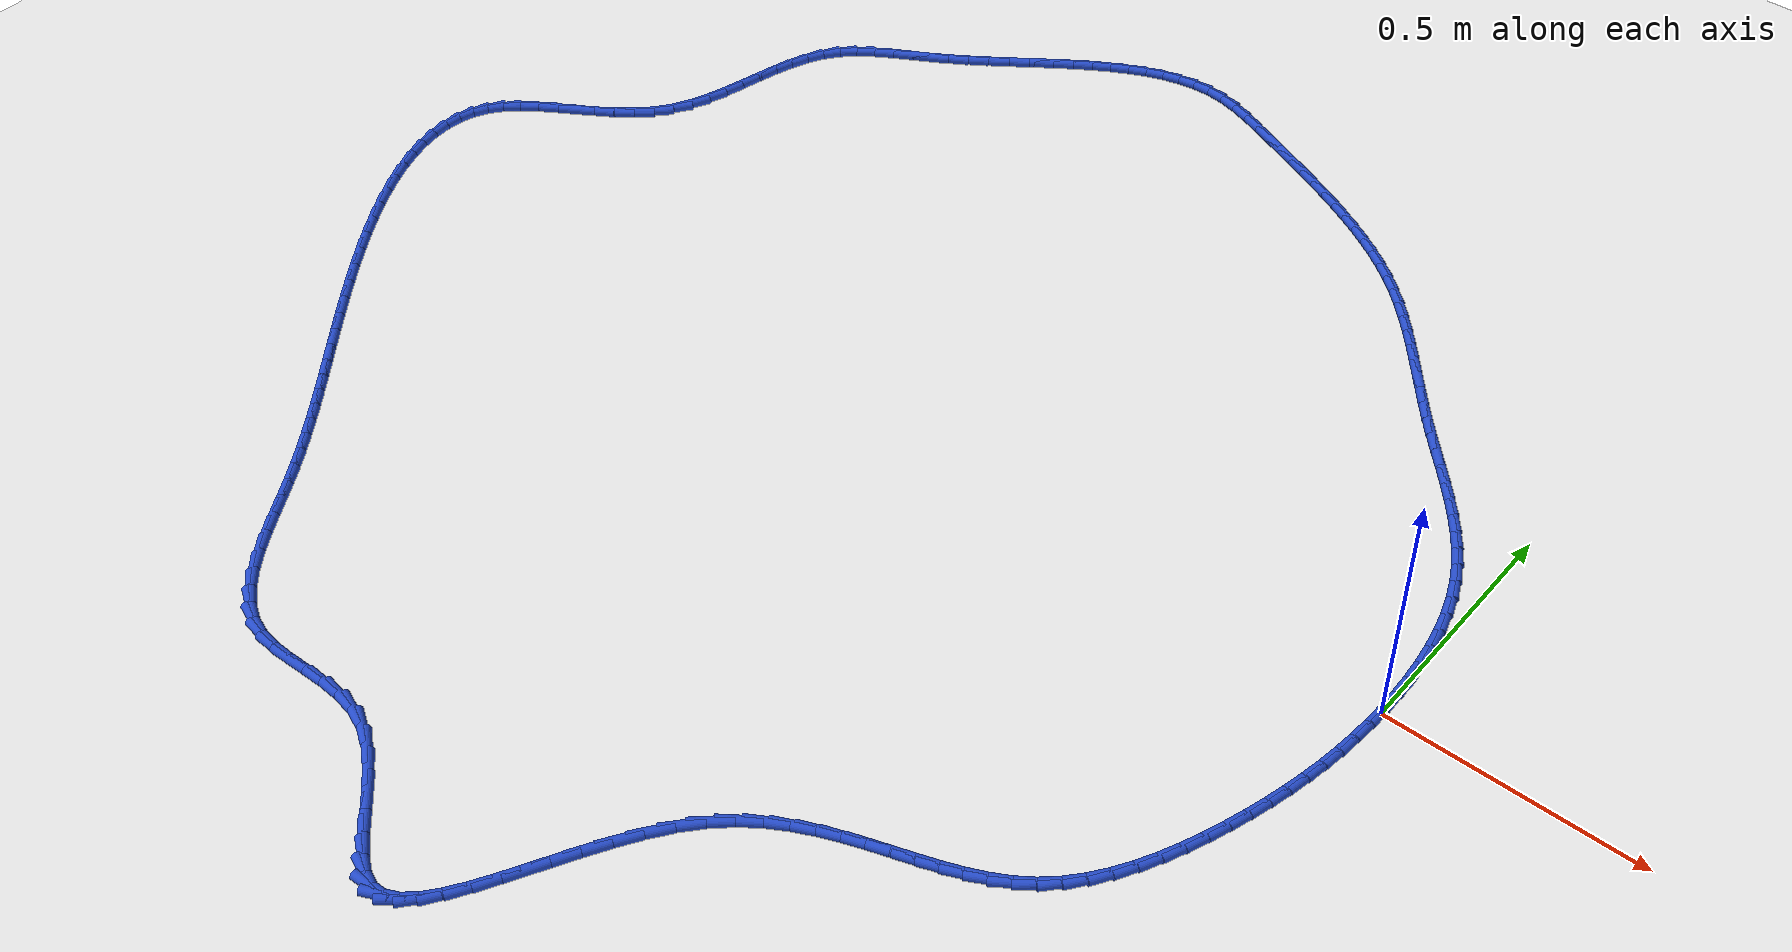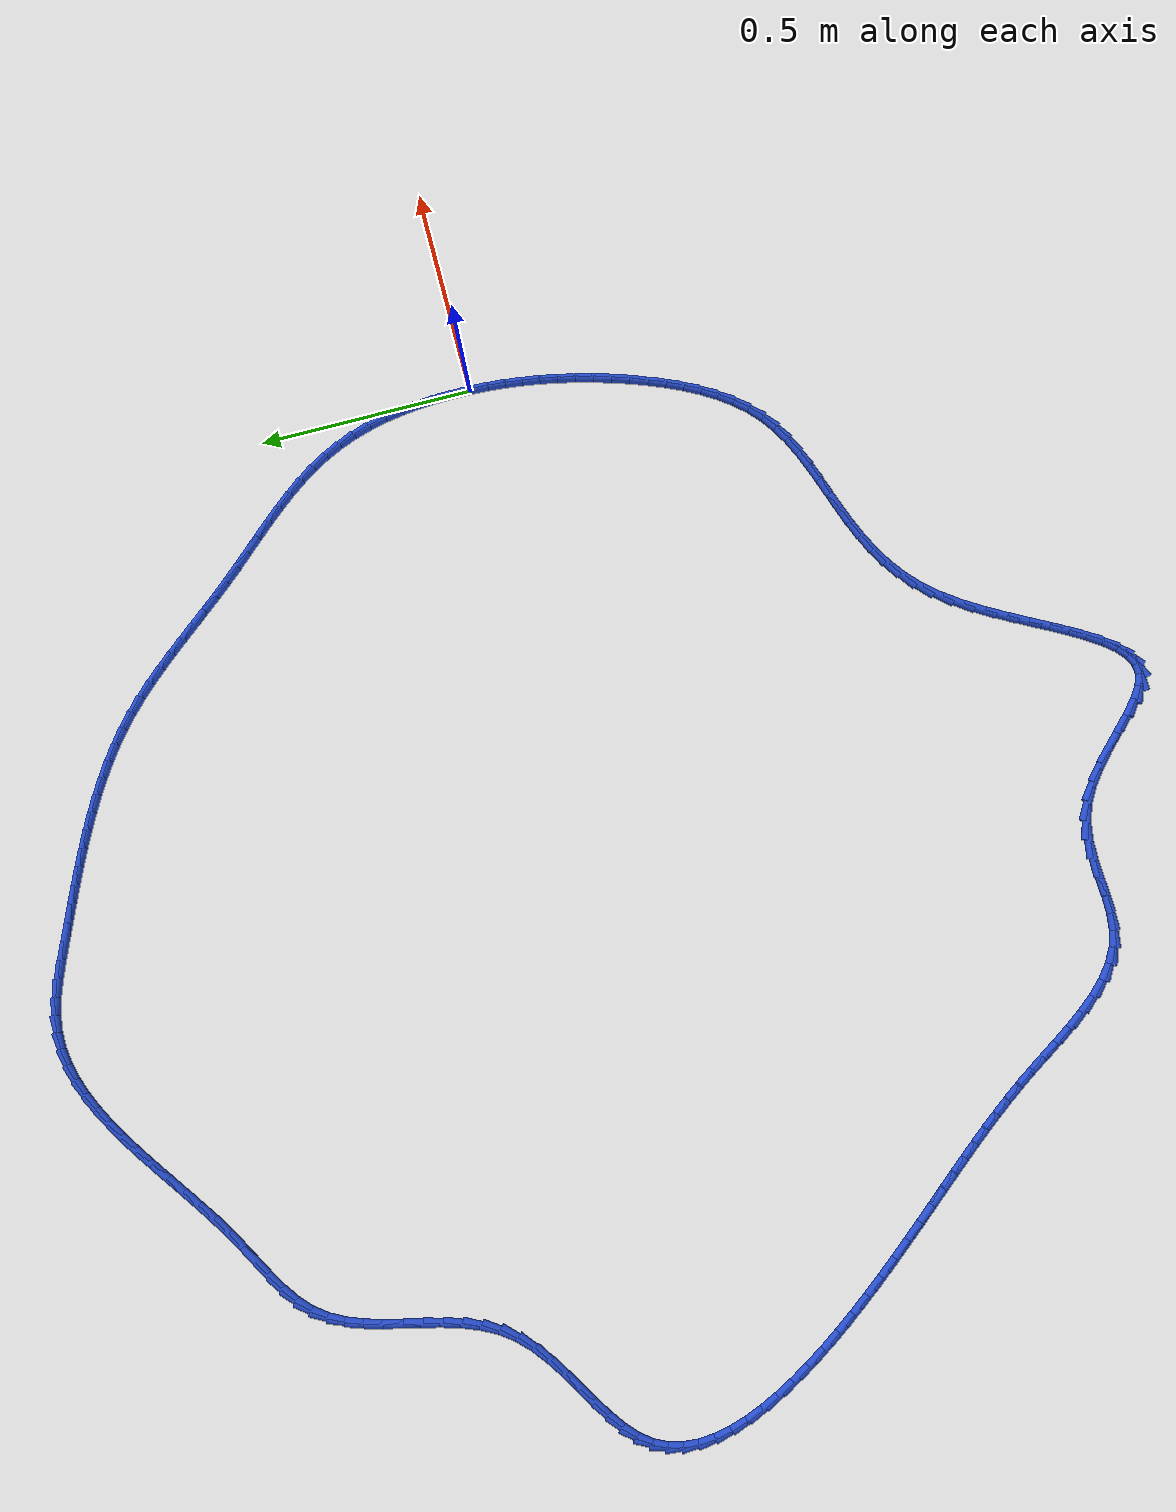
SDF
<sdf version="1.6">
 <world name="default">
  <light name="sun" type="directional">
   <pose>0 0 10 0 -0 0</pose>
   <diffuse>0.8 0.8 0.8 1</diffuse>
   <specular>0.2 0.2 0.2 1</specular>
   <attenuation>
    <range>1000</range>
    <constant>0.9</constant>
    <linear>0.01</linear>
    <quadratic>0.001</quadratic>
   </attenuation>
   <direction>-0.5 0.1 -0.9</direction>
  </light>
  <model name="ground_plane">
   <static>1</static>
   <link name="link">
    <collision name="collision">
     <geometry><plane><normal>0 0 1</normal><size>100 100</size></plane></geometry>
     <surface><friction><ode><mu>100</mu><mu2>50</mu2></ode></friction></surface>
    </collision>
    <visual name="visual">
     <cast_shadows>0</cast_shadows>
     <geometry><plane><normal>0 0 1</normal><size>100 100</size></plane></geometry>
     <material>
      <script><uri>file://media/materials/scripts/gazebo.material</uri><name>Gazebo/WhiteGlow</name></script>
     </material>
    </visual>
   </link>
  </model>
  <gravity>0 0 -9.8</gravity>
  <magnetic_field>6e-06 2.3e-05 -4.2e-05</magnetic_field>
  <atmosphere type="adiabatic"/>
  <physics name="default_physics" default="0" type="ode">
   <max_step_size>0.001</max_step_size>
   <real_time_factor>1</real_time_factor>
   <real_time_update_rate>1000</real_time_update_rate>
  </physics>
  <scene><ambient>0.4 0.4 0.4 1</ambient><background>0.7 0.7 0.7 1</background><shadows>1</shadows></scene>
  <spherical_coordinates>
   <surface_model>EARTH_WGS84</surface_model>
   <latitude_deg>0</latitude_deg>
   <longitude_deg>0</longitude_deg>
   <elevation>0</elevation>
   <heading_deg>0</heading_deg>
  </spherical_coordinates>
  <model name="line">
   <link name="link_0">
    <pose>1.5612511283791264e-17 0.0 0.01 0 1.57 1.5627371519065834</pose>
    <collision name="collision">
     <geometry><cylinder><radius>0.01</radius><length>0.08</length></cylinder></geometry>
    </collision>
    <visual name="visual">
     <material>
      <script><name>Gazebo/Blue</name><uri>file://media/materials/scripts/gazebo.material</uri></script>
     </material>
     <geometry><cylinder><radius>0.01</radius><length>0.08</length></cylinder></geometry>
    </visual>
   </link>
   <link name="link_1">
    <pose>0.00033549583603010875 0.04162815389038797 0.01 0 1.57 -1.539648303344761</pose>
    <collision name="collision">
     <geometry><cylinder><radius>0.01</radius><length>0.08</length></cylinder></geometry>
    </collision>
    <visual name="visual">
     <material>
      <script><name>Gazebo/Blue</name><uri>file://media/materials/scripts/gazebo.material</uri></script>
     </material>
     <geometry><cylinder><radius>0.01</radius><length>0.08</length></cylinder></geometry>
    </visual>
   </link>
   <link name="link_2">
    <pose>-0.0009685561631910054 0.08348089757692105 0.01 0 1.57 -1.4964898001802398</pose>
    <collision name="collision">
     <geometry><cylinder><radius>0.01</radius><length>0.08</length></cylinder></geometry>
    </collision>
    <visual name="visual">
     <material>
      <script><name>Gazebo/Blue</name><uri>file://media/materials/scripts/gazebo.material</uri></script>
     </material>
     <geometry><cylinder><radius>0.01</radius><length>0.08</length></cylinder></geometry>
    </visual>
   </link>
   <link name="link_3">
    <pose>-0.0040824264526208645 0.12530948631201214 0.01 0 1.57 -1.4488233210434356</pose>
    <collision name="collision">
     <geometry><cylinder><radius>0.01</radius><length>0.08</length></cylinder></geometry>
    </collision>
    <visual name="visual">
     <material>
      <script><name>Gazebo/Blue</name><uri>file://media/materials/scripts/gazebo.material</uri></script>
     </material>
     <geometry><cylinder><radius>0.01</radius><length>0.08</length></cylinder></geometry>
    </visual>
   </link>
   <link name="link_4">
    <pose>-0.009176385487217007 0.1668651753480741 0.01 0 1.57 -1.3960528426665788</pose>
    <collision name="collision">
     <geometry><cylinder><radius>0.01</radius><length>0.08</length></cylinder></geometry>
    </collision>
    <visual name="visual">
     <material>
      <script><name>Gazebo/Blue</name><uri>file://media/materials/scripts/gazebo.material</uri></script>
     </material>
     <geometry><cylinder><radius>0.01</radius><length>0.08</length></cylinder></geometry>
    </visual>
   </link>
   <link name="link_5">
    <pose>-0.016420703721936963 0.20789921993751986 0.01 0 1.57 -1.337561754423011</pose>
    <collision name="collision">
     <geometry><cylinder><radius>0.01</radius><length>0.08</length></cylinder></geometry>
    </collision>
    <visual name="visual">
     <material>
      <script><name>Gazebo/Blue</name><uri>file://media/materials/scripts/gazebo.material</uri></script>
     </material>
     <geometry><cylinder><radius>0.01</radius><length>0.08</length></cylinder></geometry>
    </visual>
   </link>
   <link name="link_6">
    <pose>-0.02598565161173827 0.2481628753327622 0.01 0 1.57 -1.2727487935232362</pose>
    <collision name="collision">
     <geometry><cylinder><radius>0.01</radius><length>0.08</length></cylinder></geometry>
    </collision>
    <visual name="visual">
     <material>
      <script><name>Gazebo/Blue</name><uri>file://media/materials/scripts/gazebo.material</uri></script>
     </material>
     <geometry><cylinder><radius>0.01</radius><length>0.08</length></cylinder></geometry>
    </visual>
   </link>
   <link name="link_7">
    <pose>-0.03804149961157846 0.2874073967862142 0.01 0 1.57 -1.2010875529650897</pose>
    <collision name="collision">
     <geometry><cylinder><radius>0.01</radius><length>0.08</length></cylinder></geometry>
    </collision>
    <visual name="visual">
     <material>
      <script><name>Gazebo/Blue</name><uri>file://media/materials/scripts/gazebo.material</uri></script>
     </material>
     <geometry><cylinder><radius>0.01</radius><length>0.08</length></cylinder></geometry>
    </visual>
   </link>
   <link name="link_8">
    <pose>-0.0527585181764151 0.3253840395502886 0.01 0 1.57 -1.1226983405321613</pose>
    <collision name="collision">
     <geometry><cylinder><radius>0.01</radius><length>0.08</length></cylinder></geometry>
    </collision>
    <visual name="visual">
     <material>
      <script><name>Gazebo/Blue</name><uri>file://media/materials/scripts/gazebo.material</uri></script>
     </material>
     <geometry><cylinder><radius>0.01</radius><length>0.08</length></cylinder></geometry>
    </visual>
   </link>
   <link name="link_9">
    <pose>-0.0702916352839732 0.3618573117727762 0.01 0 1.57 -1.0466355568949675</pose>
    <collision name="collision">
     <geometry><cylinder><radius>0.01</radius><length>0.08</length></cylinder></geometry>
    </collision>
    <visual name="visual">
     <material>
      <script><name>Gazebo/Blue</name><uri>file://media/materials/scripts/gazebo.material</uri></script>
     </material>
     <geometry><cylinder><radius>0.01</radius><length>0.08</length></cylinder></geometry>
    </visual>
   </link>
   <link name="link_10">
    <pose>-0.09051286786912605 0.39683610133202285 0.01 0 1.57 -0.9815511545880734</pose>
    <collision name="collision">
     <geometry><cylinder><radius>0.01</radius><length>0.08</length></cylinder></geometry>
    </collision>
    <visual name="visual">
     <material>
      <script><name>Gazebo/Blue</name><uri>file://media/materials/scripts/gazebo.material</uri></script>
     </material>
     <geometry><cylinder><radius>0.01</radius><length>0.08</length></cylinder></geometry>
    </visual>
   </link>
   <link name="link_11">
    <pose>-0.11304546967218501 0.43054417878414664 0.01 0 1.57 -0.9281302438210409</pose>
    <collision name="collision">
     <geometry><cylinder><radius>0.01</radius><length>0.08</length></cylinder></geometry>
    </collision>
    <visual name="visual">
     <material>
      <script><name>Gazebo/Blue</name><uri>file://media/materials/scripts/gazebo.material</uri></script>
     </material>
     <geometry><cylinder><radius>0.01</radius><length>0.08</length></cylinder></geometry>
    </visual>
   </link>
   <link name="link_12">
    <pose>-0.13750421696907697 0.4632126375541121 0.01 0 1.57 -0.8863381538720599</pose>
    <collision name="collision">
     <geometry><cylinder><radius>0.01</radius><length>0.08</length></cylinder></geometry>
    </collision>
    <visual name="visual">
     <material>
      <script><name>Gazebo/Blue</name><uri>file://media/materials/scripts/gazebo.material</uri></script>
     </material>
     <geometry><cylinder><radius>0.01</radius><length>0.08</length></cylinder></geometry>
    </visual>
   </link>
   <link name="link_13">
    <pose>-0.16350388603572893 0.49507257106688396 0.01 0 1.57 -0.8559054106602573</pose>
    <collision name="collision">
     <geometry><cylinder><radius>0.01</radius><length>0.08</length></cylinder></geometry>
    </collision>
    <visual name="visual">
     <material>
      <script><name>Gazebo/Blue</name><uri>file://media/materials/scripts/gazebo.material</uri></script>
     </material>
     <geometry><cylinder><radius>0.01</radius><length>0.08</length></cylinder></geometry>
    </visual>
   </link>
   <link name="link_14">
    <pose>-0.1906592531480676 0.5263550727474263 0.01 0 1.57 -0.8364956661085297</pose>
    <collision name="collision">
     <geometry><cylinder><radius>0.01</radius><length>0.08</length></cylinder></geometry>
    </collision>
    <visual name="visual">
     <material>
      <script><name>Gazebo/Blue</name><uri>file://media/materials/scripts/gazebo.material</uri></script>
     </material>
     <geometry><cylinder><radius>0.01</radius><length>0.08</length></cylinder></geometry>
    </visual>
   </link>
   <link name="link_15">
    <pose>-0.21858509458202008 0.5572912360207042 0.01 0 1.57 -0.8278171627725679</pose>
    <collision name="collision">
     <geometry><cylinder><radius>0.01</radius><length>0.08</length></cylinder></geometry>
    </collision>
    <visual name="visual">
     <material>
      <script><name>Gazebo/Blue</name><uri>file://media/materials/scripts/gazebo.material</uri></script>
     </material>
     <geometry><cylinder><radius>0.01</radius><length>0.08</length></cylinder></geometry>
    </visual>
   </link>
   <link name="link_16">
    <pose>-0.24689618661351304 0.5881121543116816 0.01 0 1.57 -0.8296854988067065</pose>
    <collision name="collision">
     <geometry><cylinder><radius>0.01</radius><length>0.08</length></cylinder></geometry>
    </collision>
    <visual name="visual">
     <material>
      <script><name>Gazebo/Blue</name><uri>file://media/materials/scripts/gazebo.material</uri></script>
     </material>
     <geometry><cylinder><radius>0.01</radius><length>0.08</length></cylinder></geometry>
    </visual>
   </link>
   <link name="link_17">
    <pose>-0.2752073055184735 0.6190489210453233 0.01 0 1.57 -0.8420476157345286</pose>
    <collision name="collision">
     <geometry><cylinder><radius>0.01</radius><length>0.08</length></cylinder></geometry>
    </collision>
    <visual name="visual">
     <material>
      <script><name>Gazebo/Blue</name><uri>file://media/materials/scripts/gazebo.material</uri></script>
     </material>
     <geometry><cylinder><radius>0.01</radius><length>0.08</length></cylinder></geometry>
    </visual>
   </link>
   <link name="link_18">
    <pose>-0.30313322798610426 0.650332629327877 0.01 0 1.57 -0.8617709014395916</pose>
    <collision name="collision">
     <geometry><cylinder><radius>0.01</radius><length>0.08</length></cylinder></geometry>
    </collision>
    <visual name="visual">
     <material>
      <script><name>Gazebo/Blue</name><uri>file://media/materials/scripts/gazebo.material</uri></script>
     </material>
     <geometry><cylinder><radius>0.01</radius><length>0.08</length></cylinder></geometry>
    </visual>
   </link>
   <link name="link_19">
    <pose>-0.3303950353820528 0.6821123904900916 0.01 0 1.57 -0.8767233830620643</pose>
    <collision name="collision">
     <geometry><cylinder><radius>0.01</radius><length>0.08</length></cylinder></geometry>
    </collision>
    <visual name="visual">
     <material>
      <script><name>Gazebo/Blue</name><uri>file://media/materials/scripts/gazebo.material</uri></script>
     </material>
     <geometry><cylinder><radius>0.01</radius><length>0.08</length></cylinder></geometry>
    </visual>
   </link>
   <link name="link_20">
    <pose>-0.35711913555311137 0.714224729571198 0.01 0 1.57 -0.8839844590462658</pose>
    <collision name="collision">
     <geometry><cylinder><radius>0.01</radius><length>0.08</length></cylinder></geometry>
    </collision>
    <visual name="visual">
     <material>
      <script><name>Gazebo/Blue</name><uri>file://media/materials/scripts/gazebo.material</uri></script>
     </material>
     <geometry><cylinder><radius>0.01</radius><length>0.08</length></cylinder></geometry>
    </visual>
   </link>
   <link name="link_21">
    <pose>-0.3835285254673263 0.7464316824353585 0.01 0 1.57 -0.8835029012207111</pose>
    <collision name="collision">
     <geometry><cylinder><radius>0.01</radius><length>0.08</length></cylinder></geometry>
    </collision>
    <visual name="visual">
     <material>
      <script><name>Gazebo/Blue</name><uri>file://media/materials/scripts/gazebo.material</uri></script>
     </material>
     <geometry><cylinder><radius>0.01</radius><length>0.08</length></cylinder></geometry>
    </visual>
   </link>
   <link name="link_22">
    <pose>-0.40984620209274397 0.7784952849467354 0.01 0 1.57 -0.8751821961282736</pose>
    <collision name="collision">
     <geometry><cylinder><radius>0.01</radius><length>0.08</length></cylinder></geometry>
    </collision>
    <visual name="visual">
     <material>
      <script><name>Gazebo/Blue</name><uri>file://media/materials/scripts/gazebo.material</uri></script>
     </material>
     <geometry><cylinder><radius>0.01</radius><length>0.08</length></cylinder></geometry>
    </visual>
   </link>
   <link name="link_23">
    <pose>-0.4362951623974108 0.8101775729694912 0.01 0 1.57 -0.8588796615535649</pose>
    <collision name="collision">
     <geometry><cylinder><radius>0.01</radius><length>0.08</length></cylinder></geometry>
    </collision>
    <visual name="visual">
     <material>
      <script><name>Gazebo/Blue</name><uri>file://media/materials/scripts/gazebo.material</uri></script>
     </material>
     <geometry><cylinder><radius>0.01</radius><length>0.08</length></cylinder></geometry>
    </visual>
   </link>
   <link name="link_24">
    <pose>-0.46309840334937274 0.841240582367788 0.01 0 1.57 -0.8344199841911342</pose>
    <collision name="collision">
     <geometry><cylinder><radius>0.01</radius><length>0.08</length></cylinder></geometry>
    </collision>
    <visual name="visual">
     <material>
      <script><name>Gazebo/Blue</name><uri>file://media/materials/scripts/gazebo.material</uri></script>
     </material>
     <geometry><cylinder><radius>0.01</radius><length>0.08</length></cylinder></geometry>
    </visual>
   </link>
   <link name="link_25">
    <pose>-0.49047892191667664 0.8714463490057884 0.01 0 1.57 -0.8016254809991757</pose>
    <collision name="collision">
     <geometry><cylinder><radius>0.01</radius><length>0.08</length></cylinder></geometry>
    </collision>
    <visual name="visual">
     <material>
      <script><name>Gazebo/Blue</name><uri>file://media/materials/scripts/gazebo.material</uri></script>
     </material>
     <geometry><cylinder><radius>0.01</radius><length>0.08</length></cylinder></geometry>
    </visual>
   </link>
   <link name="link_26">
    <pose>-0.5186597150673687 0.9005569087476553 0.01 0 1.57 -0.7603658432089958</pose>
    <collision name="collision">
     <geometry><cylinder><radius>0.01</radius><length>0.08</length></cylinder></geometry>
    </collision>
    <visual name="visual">
     <material>
      <script><name>Gazebo/Blue</name><uri>file://media/materials/scripts/gazebo.material</uri></script>
     </material>
     <geometry><cylinder><radius>0.01</radius><length>0.08</length></cylinder></geometry>
    </visual>
   </link>
   <link name="link_27">
    <pose>-0.5478637797694952 0.9283342974575503 0.01 0 1.57 -0.7109970152483571</pose>
    <collision name="collision">
     <geometry><cylinder><radius>0.01</radius><length>0.08</length></cylinder></geometry>
    </collision>
    <visual name="visual">
     <material>
      <script><name>Gazebo/Blue</name><uri>file://media/materials/scripts/gazebo.material</uri></script>
     </material>
     <geometry><cylinder><radius>0.01</radius><length>0.08</length></cylinder></geometry>
    </visual>
   </link>
   <link name="link_28">
    <pose>-0.5783044889365828 0.9545517768595727 0.01 0 1.57 -0.6601021365159226</pose>
    <collision name="collision">
     <geometry><cylinder><radius>0.01</radius><length>0.08</length></cylinder></geometry>
    </collision>
    <visual name="visual">
     <material>
      <script><name>Gazebo/Blue</name><uri>file://media/materials/scripts/gazebo.material</uri></script>
     </material>
     <geometry><cylinder><radius>0.01</radius><length>0.08</length></cylinder></geometry>
    </visual>
   </link>
   <link name="link_29">
    <pose>-0.6100279553583127 0.979177707190556 0.01 0 1.57 -0.6133875190062387</pose>
    <collision name="collision">
     <geometry><cylinder><radius>0.01</radius><length>0.08</length></cylinder></geometry>
    </collision>
    <visual name="visual">
     <material>
      <script><name>Gazebo/Blue</name><uri>file://media/materials/scripts/gazebo.material</uri></script>
     </material>
     <geometry><cylinder><radius>0.01</radius><length>0.08</length></cylinder></geometry>
    </visual>
   </link>
   <link name="link_30">
    <pose>-0.6429384966680294 1.0023458439021498 0.01 0 1.57 -0.5712090889973204</pose>
    <collision name="collision">
     <geometry><cylinder><radius>0.01</radius><length>0.08</length></cylinder></geometry>
    </collision>
    <visual name="visual">
     <material>
      <script><name>Gazebo/Blue</name><uri>file://media/materials/scripts/gazebo.material</uri></script>
     </material>
     <geometry><cylinder><radius>0.01</radius><length>0.08</length></cylinder></geometry>
    </visual>
   </link>
   <link name="link_31">
    <pose>-0.6769359430313754 1.024195176797474 0.01 0 1.57 -0.5336456454774711</pose>
    <collision name="collision">
     <geometry><cylinder><radius>0.01</radius><length>0.08</length></cylinder></geometry>
    </collision>
    <visual name="visual">
     <material>
      <script><name>Gazebo/Blue</name><uri>file://media/materials/scripts/gazebo.material</uri></script>
     </material>
     <geometry><cylinder><radius>0.01</radius><length>0.08</length></cylinder></geometry>
    </visual>
   </link>
   <link name="link_32">
    <pose>-0.7119201246139927 1.0448646956796472 0.01 0 1.57 -0.5006957187528024</pose>
    <collision name="collision">
     <geometry><cylinder><radius>0.01</radius><length>0.08</length></cylinder></geometry>
    </collision>
    <visual name="visual">
     <material>
      <script><name>Gazebo/Blue</name><uri>file://media/materials/scripts/gazebo.material</uri></script>
     </material>
     <geometry><cylinder><radius>0.01</radius><length>0.08</length></cylinder></geometry>
    </visual>
   </link>
   <link name="link_33">
    <pose>-0.7477908715815234 1.0644933903517881 0.01 0 1.57 -0.47230197898137316</pose>
    <collision name="collision">
     <geometry><cylinder><radius>0.01</radius><length>0.08</length></cylinder></geometry>
    </collision>
    <visual name="visual">
     <material>
      <script><name>Gazebo/Blue</name><uri>file://media/materials/scripts/gazebo.material</uri></script>
     </material>
     <geometry><cylinder><radius>0.01</radius><length>0.08</length></cylinder></geometry>
    </visual>
   </link>
   <link name="link_34">
    <pose>-0.7844480140996094 1.0832202506170168 0.01 0 1.57 -0.44837275368523705</pose>
    <collision name="collision">
     <geometry><cylinder><radius>0.01</radius><length>0.08</length></cylinder></geometry>
    </collision>
    <visual name="visual">
     <material>
      <script><name>Gazebo/Blue</name><uri>file://media/materials/scripts/gazebo.material</uri></script>
     </material>
     <geometry><cylinder><radius>0.01</radius><length>0.08</length></cylinder></geometry>
    </visual>
   </link>
   <link name="link_35">
    <pose>-0.8217913823338924 1.101184266278451 0.01 0 1.57 -0.4287997376437991</pose>
    <collision name="collision">
     <geometry><cylinder><radius>0.01</radius><length>0.08</length></cylinder></geometry>
    </collision>
    <visual name="visual">
     <material>
      <script><name>Gazebo/Blue</name><uri>file://media/materials/scripts/gazebo.material</uri></script>
     </material>
     <geometry><cylinder><radius>0.01</radius><length>0.08</length></cylinder></geometry>
    </visual>
   </link>
   <link name="link_36">
    <pose>-0.8597208064500153 1.118524427139211 0.01 0 1.57 -0.413471768891797</pose>
    <collision name="collision">
     <geometry><cylinder><radius>0.01</radius><length>0.08</length></cylinder></geometry>
    </collision>
    <visual name="visual">
     <material>
      <script><name>Gazebo/Blue</name><uri>file://media/materials/scripts/gazebo.material</uri></script>
     </material>
     <geometry><cylinder><radius>0.01</radius><length>0.08</length></cylinder></geometry>
    </visual>
   </link>
   <link name="link_37">
    <pose>-0.8981361166136194 1.135379723002415 0.01 0 1.57 -0.40228499665362893</pose>
    <collision name="collision">
     <geometry><cylinder><radius>0.01</radius><length>0.08</length></cylinder></geometry>
    </collision>
    <visual name="visual">
     <material>
      <script><name>Gazebo/Blue</name><uri>file://media/materials/scripts/gazebo.material</uri></script>
     </material>
     <geometry><cylinder><radius>0.01</radius><length>0.08</length></cylinder></geometry>
    </visual>
   </link>
   <link name="link_38">
    <pose>-0.9369371429903467 1.1518891436711822 0.01 0 1.57 -0.3951499590194412</pose>
    <collision name="collision">
     <geometry><cylinder><radius>0.01</radius><length>0.08</length></cylinder></geometry>
    </collision>
    <visual name="visual">
     <material>
      <script><name>Gazebo/Blue</name><uri>file://media/materials/scripts/gazebo.material</uri></script>
     </material>
     <geometry><cylinder><radius>0.01</radius><length>0.08</length></cylinder></geometry>
    </visual>
   </link>
   <link name="link_39">
    <pose>-0.9760237157458398 1.1681916789486322 0.01 0 1.57 -0.39199610895010006</pose>
    <collision name="collision">
     <geometry><cylinder><radius>0.01</radius><length>0.08</length></cylinder></geometry>
    </collision>
    <visual name="visual">
     <material>
      <script><name>Gazebo/Blue</name><uri>file://media/materials/scripts/gazebo.material</uri></script>
     </material>
     <geometry><cylinder><radius>0.01</radius><length>0.08</length></cylinder></geometry>
    </visual>
   </link>
   <link name="link_40">
    <pose>-1.01529566504574 1.1844263186378834 0.01 0 1.57 -0.391101688546585</pose>
    <collision name="collision">
     <geometry><cylinder><radius>0.01</radius><length>0.08</length></cylinder></geometry>
    </collision>
    <visual name="visual">
     <material>
      <script><name>Gazebo/Blue</name><uri>file://media/materials/scripts/gazebo.material</uri></script>
     </material>
     <geometry><cylinder><radius>0.01</radius><length>0.08</length></cylinder></geometry>
    </visual>
   </link>
   <link name="link_41">
    <pose>-1.0546501262420773 1.2006538684443004 0.01 0 1.57 -0.37277670339789604</pose>
    <collision name="collision">
     <geometry><cylinder><radius>0.01</radius><length>0.08</length></cylinder></geometry>
    </collision>
    <visual name="visual">
     <material>
      <script><name>Gazebo/Blue</name><uri>file://media/materials/scripts/gazebo.material</uri></script>
     </material>
     <geometry><cylinder><radius>0.01</radius><length>0.08</length></cylinder></geometry>
    </visual>
   </link>
   <link name="link_42">
    <pose>-1.0939528170214006 1.216023619518849 0.01 0 1.57 -0.32266676043413783</pose>
    <collision name="collision">
     <geometry><cylinder><radius>0.01</radius><length>0.08</length></cylinder></geometry>
    </collision>
    <visual name="visual">
     <material>
      <script><name>Gazebo/Blue</name><uri>file://media/materials/scripts/gazebo.material</uri></script>
     </material>
     <geometry><cylinder><radius>0.01</radius><length>0.08</length></cylinder></geometry>
    </visual>
   </link>
   <link name="link_43">
    <pose>-1.1330491425732208 1.2290955405277602 0.01 0 1.57 -0.2362228765012109</pose>
    <collision name="collision">
     <geometry><cylinder><radius>0.01</radius><length>0.08</length></cylinder></geometry>
    </collision>
    <visual name="visual">
     <material>
      <script><name>Gazebo/Blue</name><uri>file://media/materials/scripts/gazebo.material</uri></script>
     </material>
     <geometry><cylinder><radius>0.01</radius><length>0.08</length></cylinder></geometry>
    </visual>
   </link>
   <link name="link_44">
    <pose>-1.1717841676066945 1.2384197218476316 0.01 0 1.57 -0.11088151773742679</pose>
    <collision name="collision">
     <geometry><cylinder><radius>0.01</radius><length>0.08</length></cylinder></geometry>
    </collision>
    <visual name="visual">
     <material>
      <script><name>Gazebo/Blue</name><uri>file://media/materials/scripts/gazebo.material</uri></script>
     </material>
     <geometry><cylinder><radius>0.01</radius><length>0.08</length></cylinder></geometry>
    </visual>
   </link>
   <link name="link_45">
    <pose>-1.2100180524771333 1.2426766130963771 0.01 0 1.57 0.025314217034336586</pose>
    <collision name="collision">
     <geometry><cylinder><radius>0.01</radius><length>0.08</length></cylinder></geometry>
    </collision>
    <visual name="visual">
     <material>
      <script><name>Gazebo/Blue</name><uri>file://media/materials/scripts/gazebo.material</uri></script>
     </material>
     <geometry><cylinder><radius>0.01</radius><length>0.08</length></cylinder></geometry>
    </visual>
   </link>
   <link name="link_46">
    <pose>-1.2477469843669005 1.2417213306659491 0.01 0 1.57 0.15141361080776108</pose>
    <collision name="collision">
     <geometry><cylinder><radius>0.01</radius><length>0.08</length></cylinder></geometry>
    </collision>
    <visual name="visual">
     <material>
      <script><name>Gazebo/Blue</name><uri>file://media/materials/scripts/gazebo.material</uri></script>
     </material>
     <geometry><cylinder><radius>0.01</radius><length>0.08</length></cylinder></geometry>
    </visual>
   </link>
   <link name="link_47">
    <pose>-1.2850392059864337 1.2360312302268042 0.01 0 1.57 0.26301214079685964</pose>
    <collision name="collision">
     <geometry><cylinder><radius>0.01</radius><length>0.08</length></cylinder></geometry>
    </collision>
    <visual name="visual">
     <material>
      <script><name>Gazebo/Blue</name><uri>file://media/materials/scripts/gazebo.material</uri></script>
     </material>
     <geometry><cylinder><radius>0.01</radius><length>0.08</length></cylinder></geometry>
    </visual>
   </link>
   <link name="link_48">
    <pose>-1.3219636184169998 1.2260893528450796 0.01 0 1.57 0.3581972302512357</pose>
    <collision name="collision">
     <geometry><cylinder><radius>0.01</radius><length>0.08</length></cylinder></geometry>
    </collision>
    <visual name="visual">
     <material>
      <script><name>Gazebo/Blue</name><uri>file://media/materials/scripts/gazebo.material</uri></script>
     </material>
     <geometry><cylinder><radius>0.01</radius><length>0.08</length></cylinder></geometry>
    </visual>
   </link>
   <link name="link_49">
    <pose>-1.3585891227398659 1.2123787395869117 0.01 0 1.57 0.4368920691162273</pose>
    <collision name="collision">
     <geometry><cylinder><radius>0.01</radius><length>0.08</length></cylinder></geometry>
    </collision>
    <visual name="visual">
     <material>
      <script><name>Gazebo/Blue</name><uri>file://media/materials/scripts/gazebo.material</uri></script>
     </material>
     <geometry><cylinder><radius>0.01</radius><length>0.08</length></cylinder></geometry>
    </visual>
   </link>
   <link name="link_50">
    <pose>-1.3949846200362965 1.1953824315184376 0.01 0 1.57 0.5000855164081188</pose>
    <collision name="collision">
     <geometry><cylinder><radius>0.01</radius><length>0.08</length></cylinder></geometry>
    </collision>
    <visual name="visual">
     <material>
      <script><name>Gazebo/Blue</name><uri>file://media/materials/scripts/gazebo.material</uri></script>
     </material>
     <geometry><cylinder><radius>0.01</radius><length>0.08</length></cylinder></geometry>
    </visual>
   </link>
   <link name="link_51">
    <pose>-1.4312190113875587 1.1755834697057939 0.01 0 1.57 0.549187407337661</pose>
    <collision name="collision">
     <geometry><cylinder><radius>0.01</radius><length>0.08</length></cylinder></geometry>
    </collision>
    <visual name="visual">
     <material>
      <script><name>Gazebo/Blue</name><uri>file://media/materials/scripts/gazebo.material</uri></script>
     </material>
     <geometry><cylinder><radius>0.01</radius><length>0.08</length></cylinder></geometry>
    </visual>
   </link>
   <link name="link_52">
    <pose>-1.4673611978749193 1.1534648952151176 0.01 0 1.57 0.5856199729258188</pose>
    <collision name="collision">
     <geometry><cylinder><radius>0.01</radius><length>0.08</length></cylinder></geometry>
    </collision>
    <visual name="visual">
     <material>
      <script><name>Gazebo/Blue</name><uri>file://media/materials/scripts/gazebo.material</uri></script>
     </material>
     <geometry><cylinder><radius>0.01</radius><length>0.08</length></cylinder></geometry>
    </visual>
   </link>
   <link name="link_53">
    <pose>-1.5034800805796433 1.129509749112545 0.01 0 1.57 0.6106060815456396</pose>
    <collision name="collision">
     <geometry><cylinder><radius>0.01</radius><length>0.08</length></cylinder></geometry>
    </collision>
    <visual name="visual">
     <material>
      <script><name>Gazebo/Blue</name><uri>file://media/materials/scripts/gazebo.material</uri></script>
     </material>
     <geometry><cylinder><radius>0.01</radius><length>0.08</length></cylinder></geometry>
    </visual>
   </link>
   <link name="link_54">
    <pose>-1.5396445605829978 1.1042010724642133 0.01 0 1.57 0.6250806225158202</pose>
    <collision name="collision">
     <geometry><cylinder><radius>0.01</radius><length>0.08</length></cylinder></geometry>
    </collision>
    <visual name="visual">
     <material>
      <script><name>Gazebo/Blue</name><uri>file://media/materials/scripts/gazebo.material</uri></script>
     </material>
     <geometry><cylinder><radius>0.01</radius><length>0.08</length></cylinder></geometry>
    </visual>
   </link>
   <link name="link_55">
    <pose>-1.5759235389662485 1.0780219063362588 0.01 0 1.57 0.6296661046621987</pose>
    <collision name="collision">
     <geometry><cylinder><radius>0.01</radius><length>0.08</length></cylinder></geometry>
    </collision>
    <visual name="visual">
     <material>
      <script><name>Gazebo/Blue</name><uri>file://media/materials/scripts/gazebo.material</uri></script>
     </material>
     <geometry><cylinder><radius>0.01</radius><length>0.08</length></cylinder></geometry>
    </visual>
   </link>
   <link name="link_56">
    <pose>-1.6123859168106618 1.0514552917948188 0.01 0 1.57 0.6246766472419134</pose>
    <collision name="collision">
     <geometry><cylinder><radius>0.01</radius><length>0.08</length></cylinder></geometry>
    </collision>
    <visual name="visual">
     <material>
      <script><name>Gazebo/Blue</name><uri>file://media/materials/scripts/gazebo.material</uri></script>
     </material>
     <geometry><cylinder><radius>0.01</radius><length>0.08</length></cylinder></geometry>
    </visual>
   </link>
   <link name="link_57">
    <pose>-1.6491005951975033 1.0249842699060299 0.01 0 1.57 0.6101326448427539</pose>
    <collision name="collision">
     <geometry><cylinder><radius>0.01</radius><length>0.08</length></cylinder></geometry>
    </collision>
    <visual name="visual">
     <material>
      <script><name>Gazebo/Blue</name><uri>file://media/materials/scripts/gazebo.material</uri></script>
     </material>
     <geometry><cylinder><radius>0.01</radius><length>0.08</length></cylinder></geometry>
    </visual>
   </link>
   <link name="link_58">
    <pose>-1.6861364752080408 0.9990918817360284 0.01 0 1.57 0.5857806319993869</pose>
    <collision name="collision">
     <geometry><cylinder><radius>0.01</radius><length>0.08</length></cylinder></geometry>
    </collision>
    <visual name="visual">
     <material>
      <script><name>Gazebo/Blue</name><uri>file://media/materials/scripts/gazebo.material</uri></script>
     </material>
     <geometry><cylinder><radius>0.01</radius><length>0.08</length></cylinder></geometry>
    </visual>
   </link>
   <link name="link_59">
    <pose>-1.723562457923539 0.9742611683509518 0.01 0 1.57 0.5513042983160626</pose>
    <collision name="collision">
     <geometry><cylinder><radius>0.01</radius><length>0.08</length></cylinder></geometry>
    </collision>
    <visual name="visual">
     <material>
      <script><name>Gazebo/Blue</name><uri>file://media/materials/scripts/gazebo.material</uri></script>
     </material>
     <geometry><cylinder><radius>0.01</radius><length>0.08</length></cylinder></geometry>
    </visual>
   </link>
   <link name="link_60">
    <pose>-1.7614426939557197 0.9509685645470538 0.01 0 1.57 0.5212864418836666</pose>
    <collision name="collision">
     <geometry><cylinder><radius>0.01</radius><length>0.08</length></cylinder></geometry>
    </collision>
    <visual name="visual">
     <material>
      <script><name>Gazebo/Blue</name><uri>file://media/materials/scripts/gazebo.material</uri></script>
     </material>
     <geometry><cylinder><radius>0.01</radius><length>0.08</length></cylinder></geometry>
    </visual>
   </link>
   <link name="link_61">
    <pose>-1.799447845583769 0.9291432981348755 0.01 0 1.57 0.522524151788277</pose>
    <collision name="collision">
     <geometry><cylinder><radius>0.01</radius><length>0.08</length></cylinder></geometry>
    </collision>
    <visual name="visual">
     <material>
      <script><name>Gazebo/Blue</name><uri>file://media/materials/scripts/gazebo.material</uri></script>
     </material>
     <geometry><cylinder><radius>0.01</radius><length>0.08</length></cylinder></geometry>
    </visual>
   </link>
   <link name="link_62">
    <pose>-1.8365664592503095 0.9077660083138831 0.01 0 1.57 0.5600886514096115</pose>
    <collision name="collision">
     <geometry><cylinder><radius>0.01</radius><length>0.08</length></cylinder></geometry>
    </collision>
    <visual name="visual">
     <material>
      <script><name>Gazebo/Blue</name><uri>file://media/materials/scripts/gazebo.material</uri></script>
     </material>
     <geometry><cylinder><radius>0.01</radius><length>0.08</length></cylinder></geometry>
    </visual>
   </link>
   <link name="link_63">
    <pose>-1.871719070022234 0.8857227538428262 0.01 0 1.57 0.6383545939307347</pose>
    <collision name="collision">
     <geometry><cylinder><radius>0.01</radius><length>0.08</length></cylinder></geometry>
    </collision>
    <visual name="visual">
     <material>
      <script><name>Gazebo/Blue</name><uri>file://media/materials/scripts/gazebo.material</uri></script>
     </material>
     <geometry><cylinder><radius>0.01</radius><length>0.08</length></cylinder></geometry>
    </visual>
   </link>
   <link name="link_64">
    <pose>-1.9038262129664318 0.8618995934804544 0.01 0 1.57 0.7622721081351629</pose>
    <collision name="collision">
     <geometry><cylinder><radius>0.01</radius><length>0.08</length></cylinder></geometry>
    </collision>
    <visual name="visual">
     <material>
      <script><name>Gazebo/Blue</name><uri>file://media/materials/scripts/gazebo.material</uri></script>
     </material>
     <geometry><cylinder><radius>0.01</radius><length>0.08</length></cylinder></geometry>
    </visual>
   </link>
   <link name="link_65">
    <pose>-1.9318084231497958 0.8351825859855172 0.01 0 1.57 0.9291488403048755</pose>
    <collision name="collision">
     <geometry><cylinder><radius>0.01</radius><length>0.08</length></cylinder></geometry>
    </collision>
    <visual name="visual">
     <material>
      <script><name>Gazebo/Blue</name><uri>file://media/materials/scripts/gazebo.material</uri></script>
     </material>
     <geometry><cylinder><radius>0.01</radius><length>0.08</length></cylinder></geometry>
    </visual>
   </link>
   <link name="link_66">
    <pose>-1.9546931605929267 0.8045514782603879 0.01 0 1.57 1.0881359467757474</pose>
    <collision name="collision">
     <geometry><cylinder><radius>0.01</radius><length>0.08</length></cylinder></geometry>
    </collision>
    <visual name="visual">
     <material>
      <script><name>Gazebo/Blue</name><uri>file://media/materials/scripts/gazebo.material</uri></script>
     </material>
     <geometry><cylinder><radius>0.01</radius><length>0.08</length></cylinder></geometry>
    </visual>
   </link>
   <link name="link_67">
    <pose>-1.9727562121993567 0.7700798070501369 0.01 0 1.57 1.2061750852037698</pose>
    <collision name="collision">
     <geometry><cylinder><radius>0.01</radius><length>0.08</length></cylinder></geometry>
    </collision>
    <visual name="visual">
     <material>
      <script><name>Gazebo/Blue</name><uri>file://media/materials/scripts/gazebo.material</uri></script>
     </material>
     <geometry><cylinder><radius>0.01</radius><length>0.08</length></cylinder></geometry>
    </visual>
   </link>
   <link name="link_68">
    <pose>-1.9870812724670175 0.7325490015058 0.01 0 1.57 1.2852200536229144</pose>
    <collision name="collision">
     <geometry><cylinder><radius>0.01</radius><length>0.08</length></cylinder></geometry>
    </collision>
    <visual name="visual">
     <material>
      <script><name>Gazebo/Blue</name><uri>file://media/materials/scripts/gazebo.material</uri></script>
     </material>
     <geometry><cylinder><radius>0.01</radius><length>0.08</length></cylinder></geometry>
    </visual>
   </link>
   <link name="link_69">
    <pose>-1.9987656153898448 0.6927523891962072 0.01 0 1.57 1.3298440328931234</pose>
    <collision name="collision">
     <geometry><cylinder><radius>0.01</radius><length>0.08</length></cylinder></geometry>
    </collision>
    <visual name="visual">
     <material>
      <script><name>Gazebo/Blue</name><uri>file://media/materials/scripts/gazebo.material</uri></script>
     </material>
     <geometry><cylinder><radius>0.01</radius><length>0.08</length></cylinder></geometry>
    </visual>
   </link>
   <link name="link_70">
    <pose>-2.0089065149617724 0.6514832976901893 0.01 0 1.57 1.3436723399939021</pose>
    <collision name="collision">
     <geometry><cylinder><radius>0.01</radius><length>0.08</length></cylinder></geometry>
    </collision>
    <visual name="visual">
     <material>
      <script><name>Gazebo/Blue</name><uri>file://media/materials/scripts/gazebo.material</uri></script>
     </material>
     <geometry><cylinder><radius>0.01</radius><length>0.08</length></cylinder></geometry>
    </visual>
   </link>
   <link name="link_71">
    <pose>-2.0186012451767366 0.6095350545565762 0.01 0 1.57 1.3283543671889042</pose>
    <collision name="collision">
     <geometry><cylinder><radius>0.01</radius><length>0.08</length></cylinder></geometry>
    </collision>
    <visual name="visual">
     <material>
      <script><name>Gazebo/Blue</name><uri>file://media/materials/scripts/gazebo.material</uri></script>
     </material>
     <geometry><cylinder><radius>0.01</radius><length>0.08</length></cylinder></geometry>
    </visual>
   </link>
   <link name="link_72">
    <pose>-2.02894708002867 0.5677009873641989 0.01 0 1.57 1.2834637673185854</pose>
    <collision name="collision">
     <geometry><cylinder><radius>0.01</radius><length>0.08</length></cylinder></geometry>
    </collision>
    <visual name="visual">
     <material>
      <script><name>Gazebo/Blue</name><uri>file://media/materials/scripts/gazebo.material</uri></script>
     </material>
     <geometry><cylinder><radius>0.01</radius><length>0.08</length></cylinder></geometry>
    </visual>
   </link>
   <link name="link_73">
    <pose>-2.041041293511509 0.5267744236818874 0.01 0 1.57 1.206890173770978</pose>
    <collision name="collision">
     <geometry><cylinder><radius>0.01</radius><length>0.08</length></cylinder></geometry>
    </collision>
    <visual name="visual">
     <material>
      <script><name>Gazebo/Blue</name><uri>file://media/materials/scripts/gazebo.material</uri></script>
     </material>
     <geometry><cylinder><radius>0.01</radius><length>0.08</length></cylinder></geometry>
    </visual>
   </link>
   <link name="link_74">
    <pose>-2.0559811596191873 0.4875486910784713 0.01 0 1.57 1.0959520341082813</pose>
    <collision name="collision">
     <geometry><cylinder><radius>0.01</radius><length>0.08</length></cylinder></geometry>
    </collision>
    <visual name="visual">
     <material>
      <script><name>Gazebo/Blue</name><uri>file://media/materials/scripts/gazebo.material</uri></script>
     </material>
     <geometry><cylinder><radius>0.01</radius><length>0.08</length></cylinder></geometry>
    </visual>
   </link>
   <link name="link_75">
    <pose>-2.074863952345641 0.4508171171227822 0.01 0 1.57 0.950108576690911</pose>
    <collision name="collision">
     <geometry><cylinder><radius>0.01</radius><length>0.08</length></cylinder></geometry>
    </collision>
    <visual name="visual">
     <material>
      <script><name>Gazebo/Blue</name><uri>file://media/materials/scripts/gazebo.material</uri></script>
     </material>
     <geometry><cylinder><radius>0.01</radius><length>0.08</length></cylinder></geometry>
    </visual>
   </link>
   <link name="link_76">
    <pose>-2.0987784361531188 0.41736784411725986 0.01 0 1.57 0.7970377884233915</pose>
    <collision name="collision">
     <geometry><cylinder><radius>0.01</radius><length>0.08</length></cylinder></geometry>
    </collision>
    <visual name="visual">
     <material>
      <script><name>Gazebo/Blue</name><uri>file://media/materials/scripts/gazebo.material</uri></script>
     </material>
     <geometry><cylinder><radius>0.01</radius><length>0.08</length></cylinder></geometry>
    </visual>
   </link>
   <link name="link_77">
    <pose>-2.1279783183346987 0.38748017392131784 0.01 0 1.57 0.6821661035276099</pose>
    <collision name="collision">
     <geometry><cylinder><radius>0.01</radius><length>0.08</length></cylinder></geometry>
    </collision>
    <visual name="visual">
     <material>
      <script><name>Gazebo/Blue</name><uri>file://media/materials/scripts/gazebo.material</uri></script>
     </material>
     <geometry><cylinder><radius>0.01</radius><length>0.08</length></cylinder></geometry>
    </visual>
   </link>
   <link name="link_78">
    <pose>-2.161190864907318 0.36050327440608576 0.01 0 1.57 0.606274256350804</pose>
    <collision name="collision">
     <geometry><cylinder><radius>0.01</radius><length>0.08</length></cylinder></geometry>
    </collision>
    <visual name="visual">
     <material>
      <script><name>Gazebo/Blue</name><uri>file://media/materials/scripts/gazebo.material</uri></script>
     </material>
     <geometry><cylinder><radius>0.01</radius><length>0.08</length></cylinder></geometry>
    </visual>
   </link>
   <link name="link_79">
    <pose>-2.1969805783976755 0.3356871338301589 0.01 0 1.57 0.5648692213021964</pose>
    <collision name="collision">
     <geometry><cylinder><radius>0.01</radius><length>0.08</length></cylinder></geometry>
    </collision>
    <visual name="visual">
     <material>
      <script><name>Gazebo/Blue</name><uri>file://media/materials/scripts/gazebo.material</uri></script>
     </material>
     <geometry><cylinder><radius>0.01</radius><length>0.08</length></cylinder></geometry>
    </visual>
   </link>
   <link name="link_80">
    <pose>-2.233911961332468 0.3122817404521325 0.01 0 1.57 0.5555746456460561</pose>
    <collision name="collision">
     <geometry><cylinder><radius>0.01</radius><length>0.08</length></cylinder></geometry>
    </collision>
    <visual name="visual">
     <material>
      <script><name>Gazebo/Blue</name><uri>file://media/materials/scripts/gazebo.material</uri></script>
     </material>
     <geometry><cylinder><radius>0.01</radius><length>0.08</length></cylinder></geometry>
    </visual>
   </link>
   <link name="link_81">
    <pose>-2.270549516238394 0.28953708253060256 0.01 0 1.57 0.5792613284918537</pose>
    <collision name="collision">
     <geometry><cylinder><radius>0.01</radius><length>0.08</length></cylinder></geometry>
    </collision>
    <visual name="visual">
     <material>
      <script><name>Gazebo/Blue</name><uri>file://media/materials/scripts/gazebo.material</uri></script>
     </material>
     <geometry><cylinder><radius>0.01</radius><length>0.08</length></cylinder></geometry>
    </visual>
   </link>
   <link name="link_82">
    <pose>-2.3054577456421512 0.2667031483241642 0.01 0 1.57 0.6407872338526547</pose>
    <collision name="collision">
     <geometry><cylinder><radius>0.01</radius><length>0.08</length></cylinder></geometry>
    </collision>
    <visual name="visual">
     <material>
      <script><name>Gazebo/Blue</name><uri>file://media/materials/scripts/gazebo.material</uri></script>
     </material>
     <geometry><cylinder><radius>0.01</radius><length>0.08</length></cylinder></geometry>
    </visual>
   </link>
   <link name="link_83">
    <pose>-2.3372011520704383 0.2430299260914128 0.01 0 1.57 0.7495287695920162</pose>
    <collision name="collision">
     <geometry><cylinder><radius>0.01</radius><length>0.08</length></cylinder></geometry>
    </collision>
    <visual name="visual">
     <material>
      <script><name>Gazebo/Blue</name><uri>file://media/materials/scripts/gazebo.material</uri></script>
     </material>
     <geometry><cylinder><radius>0.01</radius><length>0.08</length></cylinder></geometry>
    </visual>
   </link>
   <link name="link_84">
    <pose>-2.3643442380499535 0.2177674040909443 0.01 0 1.57 0.9165470242788827</pose>
    <collision name="collision">
     <geometry><cylinder><radius>0.01</radius><length>0.08</length></cylinder></geometry>
    </collision>
    <visual name="visual">
     <material>
      <script><name>Gazebo/Blue</name><uri>file://media/materials/scripts/gazebo.material</uri></script>
     </material>
     <geometry><cylinder><radius>0.01</radius><length>0.08</length></cylinder></geometry>
    </visual>
   </link>
   <link name="link_85">
    <pose>-2.3854950760454283 0.1901888699458081 0.01 0 1.57 1.1172167058652869</pose>
    <collision name="collision">
     <geometry><cylinder><radius>0.01</radius><length>0.08</length></cylinder></geometry>
    </collision>
    <visual name="visual">
     <material>
      <script><name>Gazebo/Blue</name><uri>file://media/materials/scripts/gazebo.material</uri></script>
     </material>
     <geometry><cylinder><radius>0.01</radius><length>0.08</length></cylinder></geometry>
    </visual>
   </link>
   <link name="link_86">
    <pose>-2.4001822844450578 0.16005988039706173 0.01 0 1.57 1.310836606239151</pose>
    <collision name="collision">
     <geometry><cylinder><radius>0.01</radius><length>0.08</length></cylinder></geometry>
    </collision>
    <visual name="visual">
     <material>
      <script><name>Gazebo/Blue</name><uri>file://media/materials/scripts/gazebo.material</uri></script>
     </material>
     <geometry><cylinder><radius>0.01</radius><length>0.08</length></cylinder></geometry>
    </visual>
   </link>
   <link name="link_87">
    <pose>-2.408811873229254 0.1276151841882905 0.01 0 1.57 1.4837040635937373</pose>
    <collision name="collision">
     <geometry><cylinder><radius>0.01</radius><length>0.08</length></cylinder></geometry>
    </collision>
    <visual name="visual">
     <material>
      <script><name>Gazebo/Blue</name><uri>file://media/materials/scripts/gazebo.material</uri></script>
     </material>
     <geometry><cylinder><radius>0.01</radius><length>0.08</length></cylinder></geometry>
    </visual>
   </link>
   <link name="link_88">
    <pose>-2.411824785212504 0.0931082106687724 0.01 0 1.57 -1.5113106747101714</pose>
    <collision name="collision">
     <geometry><cylinder><radius>0.01</radius><length>0.08</length></cylinder></geometry>
    </collision>
    <visual name="visual">
     <material>
      <script><name>Gazebo/Blue</name><uri>file://media/materials/scripts/gazebo.material</uri></script>
     </material>
     <geometry><cylinder><radius>0.01</radius><length>0.08</length></cylinder></geometry>
    </visual>
   </link>
   <link name="link_89">
    <pose>-2.4096619632092935 0.05679238918778647 0.01 0 1.57 -1.39063782890287</pose>
    <collision name="collision">
     <geometry><cylinder><radius>0.01</radius><length>0.08</length></cylinder></geometry>
    </collision>
    <visual name="visual">
     <material>
      <script><name>Gazebo/Blue</name><uri>file://media/materials/scripts/gazebo.material</uri></script>
     </material>
     <geometry><cylinder><radius>0.01</radius><length>0.08</length></cylinder></geometry>
    </visual>
   </link>
   <link name="link_90">
    <pose>-2.4027643500341065 0.01892114909461071 0.01 0 1.57 -1.2925176660275774</pose>
    <collision name="collision">
     <geometry><cylinder><radius>0.01</radius><length>0.08</length></cylinder></geometry>
    </collision>
    <visual name="visual">
     <material>
      <script><name>Gazebo/Blue</name><uri>file://media/materials/scripts/gazebo.material</uri></script>
     </material>
     <geometry><cylinder><radius>0.01</radius><length>0.08</length></cylinder></geometry>
    </visual>
   </link>
   <link name="link_91">
    <pose>-2.39157288850143 -0.020252080261476554 0.01 0 1.57 -1.2128717313558188</pose>
    <collision name="collision">
     <geometry><cylinder><radius>0.01</radius><length>0.08</length></cylinder></geometry>
    </collision>
    <visual name="visual">
     <material>
      <script><name>Gazebo/Blue</name><uri>file://media/materials/scripts/gazebo.material</uri></script>
     </material>
     <geometry><cylinder><radius>0.01</radius><length>0.08</length></cylinder></geometry>
    </visual>
   </link>
   <link name="link_92">
    <pose>-2.376528521425749 -0.060473869531197766 0.01 0 1.57 -1.1479684359839162</pose>
    <collision name="collision">
     <geometry><cylinder><radius>0.01</radius><length>0.08</length></cylinder></geometry>
    </collision>
    <visual name="visual">
     <material>
      <script><name>Gazebo/Blue</name><uri>file://media/materials/scripts/gazebo.material</uri></script>
     </material>
     <geometry><cylinder><radius>0.01</radius><length>0.08</length></cylinder></geometry>
    </visual>
   </link>
   <link name="link_93">
    <pose>-2.3580721916215492 -0.10149078936527302 0.01 0 1.57 -1.0947519790368652</pose>
    <collision name="collision">
     <geometry><cylinder><radius>0.01</radius><length>0.08</length></cylinder></geometry>
    </collision>
    <visual name="visual">
     <material>
      <script><name>Gazebo/Blue</name><uri>file://media/materials/scripts/gazebo.material</uri></script>
     </material>
     <geometry><cylinder><radius>0.01</radius><length>0.08</length></cylinder></geometry>
    </visual>
   </link>
   <link name="link_94">
    <pose>-2.336644841903318 -0.1430494104144247 0.01 0 1.57 -1.0508414419755985</pose>
    <collision name="collision">
     <geometry><cylinder><radius>0.01</radius><length>0.08</length></cylinder></geometry>
    </collision>
    <visual name="visual">
     <material>
      <script><name>Gazebo/Blue</name><uri>file://media/materials/scripts/gazebo.material</uri></script>
     </material>
     <geometry><cylinder><radius>0.01</radius><length>0.08</length></cylinder></geometry>
    </visual>
   </link>
   <link name="link_95">
    <pose>-2.3126874150855388 -0.18489630332937454 0.01 0 1.57 -1.0144239967621445</pose>
    <collision name="collision">
     <geometry><cylinder><radius>0.01</radius><length>0.08</length></cylinder></geometry>
    </collision>
    <visual name="visual">
     <material>
      <script><name>Gazebo/Blue</name><uri>file://media/materials/scripts/gazebo.material</uri></script>
     </material>
     <geometry><cylinder><radius>0.01</radius><length>0.08</length></cylinder></geometry>
    </visual>
   </link>
   <link name="link_96">
    <pose>-2.286640853982698 -0.22677803876084413 0.01 0 1.57 -0.9841355612535999</pose>
    <collision name="collision">
     <geometry><cylinder><radius>0.01</radius><length>0.08</length></cylinder></geometry>
    </collision>
    <visual name="visual">
     <material>
      <script><name>Gazebo/Blue</name><uri>file://media/materials/scripts/gazebo.material</uri></script>
     </material>
     <geometry><cylinder><radius>0.01</radius><length>0.08</length></cylinder></geometry>
    </visual>
   </link>
   <link name="link_97">
    <pose>-2.2589461014092818 -0.26844118735955513 0.01 0 1.57 -0.9589598821607873</pose>
    <collision name="collision">
     <geometry><cylinder><radius>0.01</radius><length>0.08</length></cylinder></geometry>
    </collision>
    <visual name="visual">
     <material>
      <script><name>Gazebo/Blue</name><uri>file://media/materials/scripts/gazebo.material</uri></script>
     </material>
     <geometry><cylinder><radius>0.01</radius><length>0.08</length></cylinder></geometry>
    </visual>
   </link>
   <link name="link_98">
    <pose>-2.2300441001797755 -0.3096323197762302 0.01 0 1.57 -0.9381524374933521</pose>
    <collision name="collision">
     <geometry><cylinder><radius>0.01</radius><length>0.08</length></cylinder></geometry>
    </collision>
    <visual name="visual">
     <material>
      <script><name>Gazebo/Blue</name><uri>file://media/materials/scripts/gazebo.material</uri></script>
     </material>
     <geometry><cylinder><radius>0.01</radius><length>0.08</length></cylinder></geometry>
    </visual>
   </link>
   <link name="link_99">
    <pose>-2.2003757931086647 -0.350098006661589 0.01 0 1.57 -0.9211877030257429</pose>
    <collision name="collision">
     <geometry><cylinder><radius>0.01</radius><length>0.08</length></cylinder></geometry>
    </collision>
    <visual name="visual">
     <material>
      <script><name>Gazebo/Blue</name><uri>file://media/materials/scripts/gazebo.material</uri></script>
     </material>
     <geometry><cylinder><radius>0.01</radius><length>0.08</length></cylinder></geometry>
    </visual>
   </link>
   <link name="link_100">
    <pose>-2.170382123010435 -0.3895848186663543 0.01 0 1.57 -0.9077271704698503</pose>
    <collision name="collision">
     <geometry><cylinder><radius>0.01</radius><length>0.08</length></cylinder></geometry>
    </collision>
    <visual name="visual">
     <material>
      <script><name>Gazebo/Blue</name><uri>file://media/materials/scripts/gazebo.material</uri></script>
     </material>
     <geometry><cylinder><radius>0.01</radius><length>0.08</length></cylinder></geometry>
    </visual>
   </link>
   <link name="link_101">
    <pose>-2.140504032699572 -0.42783932644124767 0.01 0 1.57 -0.8976070653831654</pose>
    <collision name="collision">
     <geometry><cylinder><radius>0.01</radius><length>0.08</length></cylinder></geometry>
    </collision>
    <visual name="visual">
     <material>
      <script><name>Gazebo/Blue</name><uri>file://media/materials/scripts/gazebo.material</uri></script>
     </material>
     <geometry><cylinder><radius>0.01</radius><length>0.08</length></cylinder></geometry>
    </visual>
   </link>
   <link name="link_102">
    <pose>-2.111182464990562 -0.4646081006369909 0.01 0 1.57 -0.8906902278308524</pose>
    <collision name="collision">
     <geometry><cylinder><radius>0.01</radius><length>0.08</length></cylinder></geometry>
    </collision>
    <visual name="visual">
     <material>
      <script><name>Gazebo/Blue</name><uri>file://media/materials/scripts/gazebo.material</uri></script>
     </material>
     <geometry><cylinder><radius>0.01</radius><length>0.08</length></cylinder></geometry>
    </visual>
   </link>
   <link name="link_103">
    <pose>-2.082792959469498 -0.4997072739634089 0.01 0 1.57 -0.8863702899276745</pose>
    <collision name="collision">
     <geometry><cylinder><radius>0.01</radius><length>0.08</length></cylinder></geometry>
    </collision>
    <visual name="visual">
     <material>
      <script><name>Gazebo/Blue</name><uri>file://media/materials/scripts/gazebo.material</uri></script>
     </material>
     <geometry><cylinder><radius>0.01</radius><length>0.08</length></cylinder></geometry>
    </visual>
   </link>
   <link name="link_104">
    <pose>-2.0553563309496212 -0.5333302599805426 0.01 0 1.57 -0.884729308737887</pose>
    <collision name="collision">
     <geometry><cylinder><radius>0.01</radius><length>0.08</length></cylinder></geometry>
    </collision>
    <visual name="visual">
     <material>
      <script><name>Gazebo/Blue</name><uri>file://media/materials/scripts/gazebo.material</uri></script>
     </material>
     <geometry><cylinder><radius>0.01</radius><length>0.08</length></cylinder></geometry>
    </visual>
   </link>
   <link name="link_105">
    <pose>-2.0287736983083082 -0.5657977793549738 0.01 0 1.57 -0.8860870112374084</pose>
    <collision name="collision">
     <geometry><cylinder><radius>0.01</radius><length>0.08</length></cylinder></geometry>
    </collision>
    <visual name="visual">
     <material>
      <script><name>Gazebo/Blue</name><uri>file://media/materials/scripts/gazebo.material</uri></script>
     </material>
     <geometry><cylinder><radius>0.01</radius><length>0.08</length></cylinder></geometry>
    </visual>
   </link>
   <link name="link_106">
    <pose>-2.0029460879852126 -0.5974306510688949 0.01 0 1.57 -0.8906643496873407</pose>
    <collision name="collision">
     <geometry><cylinder><radius>0.01</radius><length>0.08</length></cylinder></geometry>
    </collision>
    <visual name="visual">
     <material>
      <script><name>Gazebo/Blue</name><uri>file://media/materials/scripts/gazebo.material</uri></script>
     </material>
     <geometry><cylinder><radius>0.01</radius><length>0.08</length></cylinder></geometry>
    </visual>
   </link>
   <link name="link_107">
    <pose>-1.9777745264199877 -0.6285496941044982 0.01 0 1.57 -0.8985513540667255</pose>
    <collision name="collision">
     <geometry><cylinder><radius>0.01</radius><length>0.08</length></cylinder></geometry>
    </collision>
    <visual name="visual">
     <material>
      <script><name>Gazebo/Blue</name><uri>file://media/materials/scripts/gazebo.material</uri></script>
     </material>
     <geometry><cylinder><radius>0.01</radius><length>0.08</length></cylinder></geometry>
    </visual>
   </link>
   <link name="link_108">
    <pose>-1.9531600400522888 -0.6594757274439771 0.01 0 1.57 -0.9096850223940357</pose>
    <collision name="collision">
     <geometry><cylinder><radius>0.01</radius><length>0.08</length></cylinder></geometry>
    </collision>
    <visual name="visual">
     <material>
      <script><name>Gazebo/Blue</name><uri>file://media/materials/scripts/gazebo.material</uri></script>
     </material>
     <geometry><cylinder><radius>0.01</radius><length>0.08</length></cylinder></geometry>
    </visual>
   </link>
   <link name="link_109">
    <pose>-1.9290036553217675 -0.6905295700695238 0.01 0 1.57 -0.9238423025257698</pose>
    <collision name="collision">
     <geometry><cylinder><radius>0.01</radius><length>0.08</length></cylinder></geometry>
    </collision>
    <visual name="visual">
     <material>
      <script><name>Gazebo/Blue</name><uri>file://media/materials/scripts/gazebo.material</uri></script>
     </material>
     <geometry><cylinder><radius>0.01</radius><length>0.08</length></cylinder></geometry>
    </visual>
   </link>
   <link name="link_110">
    <pose>-1.90520639866808 -0.7220320409633303 0.01 0 1.57 -0.9406512566346489</pose>
    <collision name="collision">
     <geometry><cylinder><radius>0.01</radius><length>0.08</length></cylinder></geometry>
    </collision>
    <visual name="visual">
     <material>
      <script><name>Gazebo/Blue</name><uri>file://media/materials/scripts/gazebo.material</uri></script>
     </material>
     <geometry><cylinder><radius>0.01</radius><length>0.08</length></cylinder></geometry>
    </visual>
   </link>
   <link name="link_111">
    <pose>-1.8816692965308788 -0.7543039591075896 0.01 0 1.57 -0.9596200463178239</pose>
    <collision name="collision">
     <geometry><cylinder><radius>0.01</radius><length>0.08</length></cylinder></geometry>
    </collision>
    <visual name="visual">
     <material>
      <script><name>Gazebo/Blue</name><uri>file://media/materials/scripts/gazebo.material</uri></script>
     </material>
     <geometry><cylinder><radius>0.01</radius><length>0.08</length></cylinder></geometry>
    </visual>
   </link>
   <link name="link_112">
    <pose>-1.8582933753498172 -0.7876661434844943 0.01 0 1.57 -0.9801795563173274</pose>
    <collision name="collision">
     <geometry><cylinder><radius>0.01</radius><length>0.08</length></cylinder></geometry>
    </collision>
    <visual name="visual">
     <material>
      <script><name>Gazebo/Blue</name><uri>file://media/materials/scripts/gazebo.material</uri></script>
     </material>
     <geometry><cylinder><radius>0.01</radius><length>0.08</length></cylinder></geometry>
    </visual>
   </link>
   <link name="link_113">
    <pose>-1.8349796615645497 -0.8224394130762369 0.01 0 1.57 -1.0005796190780625</pose>
    <collision name="collision">
     <geometry><cylinder><radius>0.01</radius><length>0.08</length></cylinder></geometry>
    </collision>
    <visual name="visual">
     <material>
      <script><name>Gazebo/Blue</name><uri>file://media/materials/scripts/gazebo.material</uri></script>
     </material>
     <geometry><cylinder><radius>0.01</radius><length>0.08</length></cylinder></geometry>
    </visual>
   </link>
   <link name="link_114">
    <pose>-1.81161655506195 -0.858871724888304 0.01 0 1.57 -1.0074506505190437</pose>
    <collision name="collision">
     <geometry><cylinder><radius>0.01</radius><length>0.08</length></cylinder></geometry>
    </collision>
    <visual name="visual">
     <material>
      <script><name>Gazebo/Blue</name><uri>file://media/materials/scripts/gazebo.material</uri></script>
     </material>
     <geometry><cylinder><radius>0.01</radius><length>0.08</length></cylinder></geometry>
    </visual>
   </link>
   <link name="link_115">
    <pose>-1.7879435188512194 -0.8963515903196585 0.01 0 1.57 -0.9933011861653044</pose>
    <collision name="collision">
     <geometry><cylinder><radius>0.01</radius><length>0.08</length></cylinder></geometry>
    </collision>
    <visual name="visual">
     <material>
      <script><name>Gazebo/Blue</name><uri>file://media/materials/scripts/gazebo.material</uri></script>
     </material>
     <geometry><cylinder><radius>0.01</radius><length>0.08</length></cylinder></geometry>
    </visual>
   </link>
   <link name="link_116">
    <pose>-1.7636028952286384 -0.9337070822040963 0.01 0 1.57 -0.9576017412209656</pose>
    <collision name="collision">
     <geometry><cylinder><radius>0.01</radius><length>0.08</length></cylinder></geometry>
    </collision>
    <visual name="visual">
     <material>
      <script><name>Gazebo/Blue</name><uri>file://media/materials/scripts/gazebo.material</uri></script>
     </material>
     <geometry><cylinder><radius>0.01</radius><length>0.08</length></cylinder></geometry>
    </visual>
   </link>
   <link name="link_117">
    <pose>-1.7382353607900283 -0.969756661391041 0.01 0 1.57 -0.8978007291827309</pose>
    <collision name="collision">
     <geometry><cylinder><radius>0.01</radius><length>0.08</length></cylinder></geometry>
    </collision>
    <visual name="visual">
     <material>
      <script><name>Gazebo/Blue</name><uri>file://media/materials/scripts/gazebo.material</uri></script>
     </material>
     <geometry><cylinder><radius>0.01</radius><length>0.08</length></cylinder></geometry>
    </visual>
   </link>
   <link name="link_118">
    <pose>-1.711481592131208 -1.0033187887299155 0.01 0 1.57 -0.8092633228967541</pose>
    <collision name="collision">
     <geometry><cylinder><radius>0.01</radius><length>0.08</length></cylinder></geometry>
    </collision>
    <visual name="visual">
     <material>
      <script><name>Gazebo/Blue</name><uri>file://media/materials/scripts/gazebo.material</uri></script>
     </material>
     <geometry><cylinder><radius>0.01</radius><length>0.08</length></cylinder></geometry>
    </visual>
   </link>
   <link name="link_119">
    <pose>-1.6829822658479994 -1.0332119250701433 0.01 0 1.57 -0.6857843163605973</pose>
    <collision name="collision">
     <geometry><cylinder><radius>0.01</radius><length>0.08</length></cylinder></geometry>
    </collision>
    <visual name="visual">
     <material>
      <script><name>Gazebo/Blue</name><uri>file://media/materials/scripts/gazebo.material</uri></script>
     </material>
     <geometry><cylinder><radius>0.01</radius><length>0.08</length></cylinder></geometry>
    </visual>
   </link>
   <link name="link_120">
    <pose>-1.6523780585362227 -1.0582545312611475 0.01 0 1.57 -0.5217479182776203</pose>
    <collision name="collision">
     <geometry><cylinder><radius>0.01</radius><length>0.08</length></cylinder></geometry>
    </collision>
    <visual name="visual">
     <material>
      <script><name>Gazebo/Blue</name><uri>file://media/materials/scripts/gazebo.material</uri></script>
     </material>
     <geometry><cylinder><radius>0.01</radius><length>0.08</length></cylinder></geometry>
    </visual>
   </link>
   <link name="link_121">
    <pose>-1.619309646791701 -1.0772650681523515 0.01 0 1.57 -0.31862766478055626</pose>
    <collision name="collision">
     <geometry><cylinder><radius>0.01</radius><length>0.08</length></cylinder></geometry>
    </collision>
    <visual name="visual">
     <material>
      <script><name>Gazebo/Blue</name><uri>file://media/materials/scripts/gazebo.material</uri></script>
     </material>
     <geometry><cylinder><radius>0.01</radius><length>0.08</length></cylinder></geometry>
    </visual>
   </link>
   <link name="link_122">
    <pose>-1.5834292522827706 -1.0891008281489225 0.01 0 1.57 -0.12931836677335584</pose>
    <collision name="collision">
     <geometry><cylinder><radius>0.01</radius><length>0.08</length></cylinder></geometry>
    </collision>
    <visual name="visual">
     <material>
      <script><name>Gazebo/Blue</name><uri>file://media/materials/scripts/gazebo.material</uri></script>
     </material>
     <geometry><cylinder><radius>0.01</radius><length>0.08</length></cylinder></geometry>
    </visual>
   </link>
   <link name="link_123">
    <pose>-1.5448352561112766 -1.0941197494845025 0.01 0 1.57 -0.012410078922640424</pose>
    <collision name="collision">
     <geometry><cylinder><radius>0.01</radius><length>0.08</length></cylinder></geometry>
    </collision>
    <visual name="visual">
     <material>
      <script><name>Gazebo/Blue</name><uri>file://media/materials/scripts/gazebo.material</uri></script>
     </material>
     <geometry><cylinder><radius>0.01</radius><length>0.08</length></cylinder></geometry>
    </visual>
   </link>
   <link name="link_124">
    <pose>-1.504204084815477 -1.094624011414405 0.01 0 1.57 0.037614399453913254</pose>
    <collision name="collision">
     <geometry><cylinder><radius>0.01</radius><length>0.08</length></cylinder></geometry>
    </collision>
    <visual name="visual">
     <material>
      <script><name>Gazebo/Blue</name><uri>file://media/materials/scripts/gazebo.material</uri></script>
     </material>
     <geometry><cylinder><radius>0.01</radius><length>0.08</length></cylinder></geometry>
    </visual>
   </link>
   <link name="link_125">
    <pose>-1.462250643017027 -1.093045213242019 0.01 0 1.57 0.028897865469953696</pose>
    <collision name="collision">
     <geometry><cylinder><radius>0.01</radius><length>0.08</length></cylinder></geometry>
    </collision>
    <visual name="visual">
     <material>
      <script><name>Gazebo/Blue</name><uri>file://media/materials/scripts/gazebo.material</uri></script>
     </material>
     <geometry><cylinder><radius>0.01</radius><length>0.08</length></cylinder></geometry>
    </visual>
   </link>
   <link name="link_126">
    <pose>-1.4196898353375793 -1.0918149542707332 0.01 0 1.57 -0.03649168953439314</pose>
    <collision name="collision">
     <geometry><cylinder><radius>0.01</radius><length>0.08</length></cylinder></geometry>
    </collision>
    <visual name="visual">
     <material>
      <script><name>Gazebo/Blue</name><uri>file://media/materials/scripts/gazebo.material</uri></script>
     </material>
     <geometry><cylinder><radius>0.01</radius><length>0.08</length></cylinder></geometry>
    </visual>
   </link>
   <link name="link_127">
    <pose>-1.3772365663987902 -1.0933648338039363 0.01 0 1.57 -0.16101252593326026</pose>
    <collision name="collision">
     <geometry><cylinder><radius>0.01</radius><length>0.08</length></cylinder></geometry>
    </collision>
    <visual name="visual">
     <material>
      <script><name>Gazebo/Blue</name><uri>file://media/materials/scripts/gazebo.material</uri></script>
     </material>
     <geometry><cylinder><radius>0.01</radius><length>0.08</length></cylinder></geometry>
    </visual>
   </link>
   <link name="link_128">
    <pose>-1.3356057408223116 -1.100126451145017 0.01 0 1.57 -0.3442833557413394</pose>
    <collision name="collision">
     <geometry><cylinder><radius>0.01</radius><length>0.08</length></cylinder></geometry>
    </collision>
    <visual name="visual">
     <material>
      <script><name>Gazebo/Blue</name><uri>file://media/materials/scripts/gazebo.material</uri></script>
     </material>
     <geometry><cylinder><radius>0.01</radius><length>0.08</length></cylinder></geometry>
    </visual>
   </link>
   <link name="link_129">
    <pose>-1.2955079276606887 -1.1145040654572707 0.01 0 1.57 -0.5346849851108917</pose>
    <collision name="collision">
     <geometry><cylinder><radius>0.01</radius><length>0.08</length></cylinder></geometry>
    </collision>
    <visual name="visual">
     <material>
      <script><name>Gazebo/Blue</name><uri>file://media/materials/scripts/gazebo.material</uri></script>
     </material>
     <geometry><cylinder><radius>0.01</radius><length>0.08</length></cylinder></geometry>
    </visual>
   </link>
   <link name="link_130">
    <pose>-1.2573667320382529 -1.1370923386397325 0.01 0 1.57 -0.6664260254208906</pose>
    <collision name="collision">
     <geometry><cylinder><radius>0.01</radius><length>0.08</length></cylinder></geometry>
    </collision>
    <visual name="visual">
     <material>
      <script><name>Gazebo/Blue</name><uri>file://media/materials/scripts/gazebo.material</uri></script>
     </material>
     <geometry><cylinder><radius>0.01</radius><length>0.08</length></cylinder></geometry>
    </visual>
   </link>
   <link name="link_131">
    <pose>-1.2211448109512841 -1.165579189306048 0.01 0 1.57 -0.7465827562947344</pose>
    <collision name="collision">
     <geometry><cylinder><radius>0.01</radius><length>0.08</length></cylinder></geometry>
    </collision>
    <visual name="visual">
     <material>
      <script><name>Gazebo/Blue</name><uri>file://media/materials/scripts/gazebo.material</uri></script>
     </material>
     <geometry><cylinder><radius>0.01</radius><length>0.08</length></cylinder></geometry>
    </visual>
   </link>
   <link name="link_132">
    <pose>-1.1867632198942513 -1.197390196603224 0.01 0 1.57 -0.7844858962034048</pose>
    <collision name="collision">
     <geometry><cylinder><radius>0.01</radius><length>0.08</length></cylinder></geometry>
    </collision>
    <visual name="visual">
     <material>
      <script><name>Gazebo/Blue</name><uri>file://media/materials/scripts/gazebo.material</uri></script>
     </material>
     <geometry><cylinder><radius>0.01</radius><length>0.08</length></cylinder></geometry>
    </visual>
   </link>
   <link name="link_133">
    <pose>-1.1541430143616205 -1.229950939678268 0.01 0 1.57 -0.7821276381332868</pose>
    <collision name="collision">
     <geometry><cylinder><radius>0.01</radius><length>0.08</length></cylinder></geometry>
    </collision>
    <visual name="visual">
     <material>
      <script><name>Gazebo/Blue</name><uri>file://media/materials/scripts/gazebo.material</uri></script>
     </material>
     <geometry><cylinder><radius>0.01</radius><length>0.08</length></cylinder></geometry>
    </visual>
   </link>
   <link name="link_134">
    <pose>-1.1232052498478589 -1.2606869976781871 0.01 0 1.57 -0.7316104999910564</pose>
    <collision name="collision">
     <geometry><cylinder><radius>0.01</radius><length>0.08</length></cylinder></geometry>
    </collision>
    <visual name="visual">
     <material>
      <script><name>Gazebo/Blue</name><uri>file://media/materials/scripts/gazebo.material</uri></script>
     </material>
     <geometry><cylinder><radius>0.01</radius><length>0.08</length></cylinder></geometry>
    </visual>
   </link>
   <link name="link_135">
    <pose>-1.0938709818474337 -1.2870239497499887 0.01 0 1.57 -0.6082268007498983</pose>
    <collision name="collision">
     <geometry><cylinder><radius>0.01</radius><length>0.08</length></cylinder></geometry>
    </collision>
    <visual name="visual">
     <material>
      <script><name>Gazebo/Blue</name><uri>file://media/materials/scripts/gazebo.material</uri></script>
     </material>
     <geometry><cylinder><radius>0.01</radius><length>0.08</length></cylinder></geometry>
    </visual>
   </link>
   <link name="link_136">
    <pose>-1.0660612658548116 -1.30638737504068 0.01 0 1.57 -0.3564899322293992</pose>
    <collision name="collision">
     <geometry><cylinder><radius>0.01</radius><length>0.08</length></cylinder></geometry>
    </collision>
    <visual name="visual">
     <material>
      <script><name>Gazebo/Blue</name><uri>file://media/materials/scripts/gazebo.material</uri></script>
     </material>
     <geometry><cylinder><radius>0.01</radius><length>0.08</length></cylinder></geometry>
    </visual>
   </link>
   <link name="link_137">
    <pose>-1.039697019515341 -1.316205440196598 0.01 0 1.57 0.05177253403404898</pose>
    <collision name="collision">
     <geometry><cylinder><radius>0.01</radius><length>0.08</length></cylinder></geometry>
    </collision>
    <visual name="visual">
     <material>
      <script><name>Gazebo/Blue</name><uri>file://media/materials/scripts/gazebo.material</uri></script>
     </material>
     <geometry><cylinder><radius>0.01</radius><length>0.08</length></cylinder></geometry>
    </visual>
   </link>
   <link name="link_138">
    <pose>-1.014645831906322 -1.3149073166981777 0.01 0 1.57 0.44586157536714677</pose>
    <collision name="collision">
     <geometry><cylinder><radius>0.01</radius><length>0.08</length></cylinder></geometry>
    </collision>
    <visual name="visual">
     <material>
      <script><name>Gazebo/Blue</name><uri>file://media/materials/scripts/gazebo.material</uri></script>
     </material>
     <geometry><cylinder><radius>0.01</radius><length>0.08</length></cylinder></geometry>
    </visual>
   </link>
   <link name="link_139">
    <pose>-0.990641465915255 -1.3034341628992614 0.01 0 1.57 0.7183523614605639</pose>
    <collision name="collision">
     <geometry><cylinder><radius>0.01</radius><length>0.08</length></cylinder></geometry>
    </collision>
    <visual name="visual">
     <material>
      <script><name>Gazebo/Blue</name><uri>file://media/materials/scripts/gazebo.material</uri></script>
     </material>
     <geometry><cylinder><radius>0.01</radius><length>0.08</length></cylinder></geometry>
    </visual>
   </link>
   <link name="link_140">
    <pose>-0.9673970277336992 -1.2831148740318956 0.01 0 1.57 0.8851515519122033</pose>
    <collision name="collision">
     <geometry><cylinder><radius>0.01</radius><length>0.08</length></cylinder></geometry>
    </collision>
    <visual name="visual">
     <material>
      <script><name>Gazebo/Blue</name><uri>file://media/materials/scripts/gazebo.material</uri></script>
     </material>
     <geometry><cylinder><radius>0.01</radius><length>0.08</length></cylinder></geometry>
    </visual>
   </link>
   <link name="link_141">
    <pose>-0.9446256235532129 -1.2552783453281275 0.01 0 1.57 0.9847900828310036</pose>
    <collision name="collision">
     <geometry><cylinder><radius>0.01</radius><length>0.08</length></cylinder></geometry>
    </collision>
    <visual name="visual">
     <material>
      <script><name>Gazebo/Blue</name><uri>file://media/materials/scripts/gazebo.material</uri></script>
     </material>
     <geometry><cylinder><radius>0.01</radius><length>0.08</length></cylinder></geometry>
    </visual>
   </link>
   <link name="link_142">
    <pose>-0.9220403595653551 -1.221253472020004 0.01 0 1.57 1.0426547988320063</pose>
    <collision name="collision">
     <geometry><cylinder><radius>0.01</radius><length>0.08</length></cylinder></geometry>
    </collision>
    <visual name="visual">
     <material>
      <script><name>Gazebo/Blue</name><uri>file://media/materials/scripts/gazebo.material</uri></script>
     </material>
     <geometry><cylinder><radius>0.01</radius><length>0.08</length></cylinder></geometry>
    </visual>
   </link>
   <link name="link_143">
    <pose>-0.8993543419616853 -1.1823691493395718 0.01 0 1.57 1.072571818351298</pose>
    <collision name="collision">
     <geometry><cylinder><radius>0.01</radius><length>0.08</length></cylinder></geometry>
    </collision>
    <visual name="visual">
     <material>
      <script><name>Gazebo/Blue</name><uri>file://media/materials/scripts/gazebo.material</uri></script>
     </material>
     <geometry><cylinder><radius>0.01</radius><length>0.08</length></cylinder></geometry>
    </visual>
   </link>
   <link name="link_144">
    <pose>-0.876280676933762 -1.1399542725188783 0.01 0 1.57 1.0816643775864334</pose>
    <collision name="collision">
     <geometry><cylinder><radius>0.01</radius><length>0.08</length></cylinder></geometry>
    </collision>
    <visual name="visual">
     <material>
      <script><name>Gazebo/Blue</name><uri>file://media/materials/scripts/gazebo.material</uri></script>
     </material>
     <geometry><cylinder><radius>0.01</radius><length>0.08</length></cylinder></geometry>
    </visual>
   </link>
   <link name="link_145">
    <pose>-0.8525324706731441 -1.0953377367899693 0.01 0 1.57 1.0731913119517629</pose>
    <collision name="collision">
     <geometry><cylinder><radius>0.01</radius><length>0.08</length></cylinder></geometry>
    </collision>
    <visual name="visual">
     <material>
      <script><name>Gazebo/Blue</name><uri>file://media/materials/scripts/gazebo.material</uri></script>
     </material>
     <geometry><cylinder><radius>0.01</radius><length>0.08</length></cylinder></geometry>
    </visual>
   </link>
   <link name="link_146">
    <pose>-0.8278228293713905 -1.049848437384893 0.01 0 1.57 1.0478963418633198</pose>
    <collision name="collision">
     <geometry><cylinder><radius>0.01</radius><length>0.08</length></cylinder></geometry>
    </collision>
    <visual name="visual">
     <material>
      <script><name>Gazebo/Blue</name><uri>file://media/materials/scripts/gazebo.material</uri></script>
     </material>
     <geometry><cylinder><radius>0.01</radius><length>0.08</length></cylinder></geometry>
    </visual>
   </link>
   <link name="link_147">
    <pose>-0.8018648592200595 -1.0048152695356947 0.01 0 1.57 1.0045338481980246</pose>
    <collision name="collision">
     <geometry><cylinder><radius>0.01</radius><length>0.08</length></cylinder></geometry>
    </collision>
    <visual name="visual">
     <material>
      <script><name>Gazebo/Blue</name><uri>file://media/materials/scripts/gazebo.material</uri></script>
     </material>
     <geometry><cylinder><radius>0.01</radius><length>0.08</length></cylinder></geometry>
    </visual>
   </link>
   <link name="link_148">
    <pose>-0.7743716664107103 -0.9615671284744212 0.01 0 1.57 0.9399369486222271</pose>
    <collision name="collision">
     <geometry><cylinder><radius>0.01</radius><length>0.08</length></cylinder></geometry>
    </collision>
    <visual name="visual">
     <material>
      <script><name>Gazebo/Blue</name><uri>file://media/materials/scripts/gazebo.material</uri></script>
     </material>
     <geometry><cylinder><radius>0.01</radius><length>0.08</length></cylinder></geometry>
    </visual>
   </link>
   <link name="link_149">
    <pose>-0.7450563571349023 -0.921432909433121 0.01 0 1.57 0.8489467747873903</pose>
    <collision name="collision">
     <geometry><cylinder><radius>0.01</radius><length>0.08</length></cylinder></geometry>
    </collision>
    <visual name="visual">
     <material>
      <script><name>Gazebo/Blue</name><uri>file://media/materials/scripts/gazebo.material</uri></script>
     </material>
     <geometry><cylinder><radius>0.01</radius><length>0.08</length></cylinder></geometry>
    </visual>
   </link>
   <link name="link_150">
    <pose>-0.7136329928341922 -0.8857385564966411 0.01 0 1.57 0.7368903146429001</pose>
    <collision name="collision">
     <geometry><cylinder><radius>0.01</radius><length>0.08</length></cylinder></geometry>
    </collision>
    <visual name="visual">
     <material>
      <script><name>Gazebo/Blue</name><uri>file://media/materials/scripts/gazebo.material</uri></script>
     </material>
     <geometry><cylinder><radius>0.01</radius><length>0.08</length></cylinder></geometry>
    </visual>
   </link>
   <link name="link_151">
    <pose>-0.6800051466051475 -0.8552245368684553 0.01 0 1.57 0.6297770201234592</pose>
    <collision name="collision">
     <geometry><cylinder><radius>0.01</radius><length>0.08</length></cylinder></geometry>
    </collision>
    <visual name="visual">
     <material>
      <script><name>Gazebo/Blue</name><uri>file://media/materials/scripts/gazebo.material</uri></script>
     </material>
     <geometry><cylinder><radius>0.01</radius><length>0.08</length></cylinder></geometry>
    </visual>
   </link>
   <link name="link_152">
    <pose>-0.6444930038639333 -0.829344236587523 0.01 0 1.57 0.5354774264680113</pose>
    <collision name="collision">
     <geometry><cylinder><radius>0.01</radius><length>0.08</length></cylinder></geometry>
    </collision>
    <visual name="visual">
     <material>
      <script><name>Gazebo/Blue</name><uri>file://media/materials/scripts/gazebo.material</uri></script>
     </material>
     <geometry><cylinder><radius>0.01</radius><length>0.08</length></cylinder></geometry>
    </visual>
   </link>
   <link name="link_153">
    <pose>-0.6074721698729595 -0.8073798277442819 0.01 0 1.57 0.457113548199906</pose>
    <collision name="collision">
     <geometry><cylinder><radius>0.01</radius><length>0.08</length></cylinder></geometry>
    </collision>
    <visual name="visual">
     <material>
      <script><name>Gazebo/Blue</name><uri>file://media/materials/scripts/gazebo.material</uri></script>
     </material>
     <geometry><cylinder><radius>0.01</radius><length>0.08</length></cylinder></geometry>
    </visual>
   </link>
   <link name="link_154">
    <pose>-0.5693182498946338 -0.7886134824291683 0.01 0 1.57 0.39638915810451597</pose>
    <collision name="collision">
     <geometry><cylinder><radius>0.01</radius><length>0.08</length></cylinder></geometry>
    </collision>
    <visual name="visual">
     <material>
      <script><name>Gazebo/Blue</name><uri>file://media/materials/scripts/gazebo.material</uri></script>
     </material>
     <geometry><cylinder><radius>0.01</radius><length>0.08</length></cylinder></geometry>
    </visual>
   </link>
   <link name="link_155">
    <pose>-0.5304068491913677 -0.7723273727326216 0.01 0 1.57 0.3540483504476811</pose>
    <collision name="collision">
     <geometry><cylinder><radius>0.01</radius><length>0.08</length></cylinder></geometry>
    </collision>
    <visual name="visual">
     <material>
      <script><name>Gazebo/Blue</name><uri>file://media/materials/scripts/gazebo.material</uri></script>
     </material>
     <geometry><cylinder><radius>0.01</radius><length>0.08</length></cylinder></geometry>
    </visual>
   </link>
   <link name="link_156">
    <pose>-0.49111357302556957 -0.7578036707450785 0.01 0 1.57 0.3304110136726524</pose>
    <collision name="collision">
     <geometry><cylinder><radius>0.01</radius><length>0.08</length></cylinder></geometry>
    </collision>
    <visual name="visual">
     <material>
      <script><name>Gazebo/Blue</name><uri>file://media/materials/scripts/gazebo.material</uri></script>
     </material>
     <geometry><cylinder><radius>0.01</radius><length>0.08</length></cylinder></geometry>
    </visual>
   </link>
   <link name="link_157">
    <pose>-0.4518140266596487 -0.7443245485569765 0.01 0 1.57 0.3258053837161615</pose>
    <collision name="collision">
     <geometry><cylinder><radius>0.01</radius><length>0.08</length></cylinder></geometry>
    </collision>
    <visual name="visual">
     <material>
      <script><name>Gazebo/Blue</name><uri>file://media/materials/scripts/gazebo.material</uri></script>
     </material>
     <geometry><cylinder><radius>0.01</radius><length>0.08</length></cylinder></geometry>
    </visual>
   </link>
   <link name="link_158">
    <pose>-0.41288381535601465 -0.7311721782587536 0.01 0 1.57 0.34083552897804126</pose>
    <collision name="collision">
     <geometry><cylinder><radius>0.01</radius><length>0.08</length></cylinder></geometry>
    </collision>
    <visual name="visual">
     <material>
      <script><name>Gazebo/Blue</name><uri>file://media/materials/scripts/gazebo.material</uri></script>
     </material>
     <geometry><cylinder><radius>0.01</radius><length>0.08</length></cylinder></geometry>
    </visual>
   </link>
   <link name="link_159">
    <pose>-0.37469854437707595 -0.7176287319408468 0.01 0 1.57 0.37646359845892824</pose>
    <collision name="collision">
     <geometry><cylinder><radius>0.01</radius><length>0.08</length></cylinder></geometry>
    </collision>
    <visual name="visual">
     <material>
      <script><name>Gazebo/Blue</name><uri>file://media/materials/scripts/gazebo.material</uri></script>
     </material>
     <geometry><cylinder><radius>0.01</radius><length>0.08</length></cylinder></geometry>
    </visual>
   </link>
   <link name="link_160">
    <pose>-0.3376338189852433 -0.7029763816936939 0.01 0 1.57 0.4338627351498992</pose>
    <collision name="collision">
     <geometry><cylinder><radius>0.01</radius><length>0.08</length></cylinder></geometry>
    </collision>
    <visual name="visual">
     <material>
      <script><name>Gazebo/Blue</name><uri>file://media/materials/scripts/gazebo.material</uri></script>
     </material>
     <geometry><cylinder><radius>0.01</radius><length>0.08</length></cylinder></geometry>
    </visual>
   </link>
   <link name="link_161">
    <pose>-0.3020652444429254 -0.6864972996077329 0.01 0 1.57 0.5139476838366134</pose>
    <collision name="collision">
     <geometry><cylinder><radius>0.01</radius><length>0.08</length></cylinder></geometry>
    </collision>
    <visual name="visual">
     <material>
      <script><name>Gazebo/Blue</name><uri>file://media/materials/scripts/gazebo.material</uri></script>
     </material>
     <geometry><cylinder><radius>0.01</radius><length>0.08</length></cylinder></geometry>
    </visual>
   </link>
   <link name="link_162">
    <pose>-0.2683684260125315 -0.6674736577734007 0.01 0 1.57 0.6164944745221506</pose>
    <collision name="collision">
     <geometry><cylinder><radius>0.01</radius><length>0.08</length></cylinder></geometry>
    </collision>
    <visual name="visual">
     <material>
      <script><name>Gazebo/Blue</name><uri>file://media/materials/scripts/gazebo.material</uri></script>
     </material>
     <geometry><cylinder><radius>0.01</radius><length>0.08</length></cylinder></geometry>
    </visual>
   </link>
   <link name="link_163">
    <pose>-0.23691896895647116 -0.6451876282811355 0.01 0 1.57 0.7349925713290207</pose>
    <collision name="collision">
     <geometry><cylinder><radius>0.01</radius><length>0.08</length></cylinder></geometry>
    </collision>
    <visual name="visual">
     <material>
      <script><name>Gazebo/Blue</name><uri>file://media/materials/scripts/gazebo.material</uri></script>
     </material>
     <geometry><cylinder><radius>0.01</radius><length>0.08</length></cylinder></geometry>
    </visual>
   </link>
   <link name="link_164">
    <pose>-0.2080276712293696 -0.6190713696035326 0.01 0 1.57 0.8448052097673882</pose>
    <collision name="collision">
     <geometry><cylinder><radius>0.01</radius><length>0.08</length></cylinder></geometry>
    </collision>
    <visual name="visual">
     <material>
      <script><name>Gazebo/Blue</name><uri>file://media/materials/scripts/gazebo.material</uri></script>
     </material>
     <geometry><cylinder><radius>0.01</radius><length>0.08</length></cylinder></geometry>
    </visual>
   </link>
   <link name="link_165">
    <pose>-0.18165635174285447 -0.5893646976502591 0.01 0 1.57 0.9387825633972622</pose>
    <collision name="collision">
     <geometry><cylinder><radius>0.01</radius><length>0.08</length></cylinder></geometry>
    </collision>
    <visual name="visual">
     <material>
      <script><name>Gazebo/Blue</name><uri>file://media/materials/scripts/gazebo.material</uri></script>
     </material>
     <geometry><cylinder><radius>0.01</radius><length>0.08</length></cylinder></geometry>
    </visual>
   </link>
   <link name="link_166">
    <pose>-0.15764988012076647 -0.5565780891741993 0.01 0 1.57 1.0183338912129576</pose>
    <collision name="collision">
     <geometry><cylinder><radius>0.01</radius><length>0.08</length></cylinder></geometry>
    </collision>
    <visual name="visual">
     <material>
      <script><name>Gazebo/Blue</name><uri>file://media/materials/scripts/gazebo.material</uri></script>
     </material>
     <geometry><cylinder><radius>0.01</radius><length>0.08</length></cylinder></geometry>
    </visual>
   </link>
   <link name="link_167">
    <pose>-0.13585304131474724 -0.5212222168888004 0.01 0 1.57 1.0852599736701192</pose>
    <collision name="collision">
     <geometry><cylinder><radius>0.01</radius><length>0.08</length></cylinder></geometry>
    </collision>
    <visual name="visual">
     <material>
      <script><name>Gazebo/Blue</name><uri>file://media/materials/scripts/gazebo.material</uri></script>
     </material>
     <geometry><cylinder><radius>0.01</radius><length>0.08</length></cylinder></geometry>
    </visual>
   </link>
   <link name="link_168">
    <pose>-0.11611062027643874 -0.4838077535075102 0.01 0 1.57 1.1413424869747353</pose>
    <collision name="collision">
     <geometry><cylinder><radius>0.01</radius><length>0.08</length></cylinder></geometry>
    </collision>
    <visual name="visual">
     <material>
      <script><name>Gazebo/Blue</name><uri>file://media/materials/scripts/gazebo.material</uri></script>
     </material>
     <geometry><cylinder><radius>0.01</radius><length>0.08</length></cylinder></geometry>
    </visual>
   </link>
   <link name="link_169">
    <pose>-0.09826740195748304 -0.44484537174377603 0.01 0 1.57 1.1881499630543153</pose>
    <collision name="collision">
     <geometry><cylinder><radius>0.01</radius><length>0.08</length></cylinder></geometry>
    </collision>
    <visual name="visual">
     <material>
      <script><name>Gazebo/Blue</name><uri>file://media/materials/scripts/gazebo.material</uri></script>
     </material>
     <geometry><cylinder><radius>0.01</radius><length>0.08</length></cylinder></geometry>
    </visual>
   </link>
   <link name="link_170">
    <pose>-0.08216817130952192 -0.404845744311045 0.01 0 1.57 1.2269669559607816</pose>
    <collision name="collision">
     <geometry><cylinder><radius>0.01</radius><length>0.08</length></cylinder></geometry>
    </collision>
    <visual name="visual">
     <material>
      <script><name>Gazebo/Blue</name><uri>file://media/materials/scripts/gazebo.material</uri></script>
     </material>
     <geometry><cylinder><radius>0.01</radius><length>0.08</length></cylinder></geometry>
    </visual>
   </link>
   <link name="link_171">
    <pose>-0.06765771328419805 -0.36431954392276633 0.01 0 1.57 1.2589044806969178</pose>
    <collision name="collision">
     <geometry><cylinder><radius>0.01</radius><length>0.08</length></cylinder></geometry>
    </collision>
    <visual name="visual">
     <material>
      <script><name>Gazebo/Blue</name><uri>file://media/materials/scripts/gazebo.material</uri></script>
     </material>
     <geometry><cylinder><radius>0.01</radius><length>0.08</length></cylinder></geometry>
    </visual>
   </link>
   <link name="link_172">
    <pose>-0.054583400057776746 -0.32376831722347493 0.01 0 1.57 1.288183372163451</pose>
    <collision name="collision">
     <geometry><cylinder><radius>0.01</radius><length>0.08</length></cylinder></geometry>
    </collision>
    <visual name="visual">
     <material>
      <script><name>Gazebo/Blue</name><uri>file://media/materials/scripts/gazebo.material</uri></script>
     </material>
     <geometry><cylinder><radius>0.01</radius><length>0.08</length></cylinder></geometry>
    </visual>
   </link>
   <link name="link_173">
    <pose>-0.04286852347226676 -0.283425814975196 0.01 0 1.57 1.3189317259924247</pose>
    <collision name="collision">
     <geometry><cylinder><radius>0.01</radius><length>0.08</length></cylinder></geometry>
    </collision>
    <visual name="visual">
     <material>
      <script><name>Gazebo/Blue</name><uri>file://media/materials/scripts/gazebo.material</uri></script>
     </material>
     <geometry><cylinder><radius>0.01</radius><length>0.08</length></cylinder></geometry>
    </visual>
   </link>
   <link name="link_174">
    <pose>-0.03252271656595446 -0.2432212315825477 0.01 0 1.57 1.3511945742643985</pose>
    <collision name="collision">
     <geometry><cylinder><radius>0.01</radius><length>0.08</length></cylinder></geometry>
    </collision>
    <visual name="visual">
     <material>
      <script><name>Gazebo/Blue</name><uri>file://media/materials/scripts/gazebo.material</uri></script>
     </material>
     <geometry><cylinder><radius>0.01</radius><length>0.08</length></cylinder></geometry>
    </visual>
   </link>
   <link name="link_175">
    <pose>-0.02356029472471072 -0.20306724513133556 0.01 0 1.57 1.384752303201363</pose>
    <collision name="collision">
     <geometry><cylinder><radius>0.01</radius><length>0.08</length></cylinder></geometry>
    </collision>
    <visual name="visual">
     <material>
      <script><name>Gazebo/Blue</name><uri>file://media/materials/scripts/gazebo.material</uri></script>
     </material>
     <geometry><cylinder><radius>0.01</radius><length>0.08</length></cylinder></geometry>
    </visual>
   </link>
   <link name="link_176">
    <pose>-0.015995573334406224 -0.1628765337073639 0.01 0 1.57 1.4193482426146153</pose>
    <collision name="collision">
     <geometry><cylinder><radius>0.01</radius><length>0.08</length></cylinder></geometry>
    </collision>
    <visual name="visual">
     <material>
      <script><name>Gazebo/Blue</name><uri>file://media/materials/scripts/gazebo.material</uri></script>
     </material>
     <geometry><cylinder><radius>0.01</radius><length>0.08</length></cylinder></geometry>
    </visual>
   </link>
   <link name="link_177">
    <pose>-0.009842867780912154 -0.12256177539643975 0.01 0 1.57 1.4546954480309104</pose>
    <collision name="collision">
     <geometry><cylinder><radius>0.01</radius><length>0.08</length></cylinder></geometry>
    </collision>
    <visual name="visual">
     <material>
      <script><name>Gazebo/Blue</name><uri>file://media/materials/scripts/gazebo.material</uri></script>
     </material>
     <geometry><cylinder><radius>0.01</radius><length>0.08</length></cylinder></geometry>
    </visual>
   </link>
   <link name="link_178">
    <pose>-0.005116493450099187 -0.08203564828436752 0.01 0 1.57 1.4904858492065363</pose>
    <collision name="collision">
     <geometry><cylinder><radius>0.01</radius><length>0.08</length></cylinder></geometry>
    </collision>
    <visual name="visual">
     <material>
      <script><name>Gazebo/Blue</name><uri>file://media/materials/scripts/gazebo.material</uri></script>
     </material>
     <geometry><cylinder><radius>0.01</radius><length>0.08</length></cylinder></geometry>
    </visual>
   </link>
   <link name="link_179">
    <pose>-0.0018307657278381776 -0.04121083045695249 0.01 0 1.57 1.5264011331733467</pose>
    <collision name="collision">
     <geometry><cylinder><radius>0.01</radius><length>0.08</length></cylinder></geometry>
    </collision>
    <visual name="visual">
     <material>
      <script><name>Gazebo/Blue</name><uri>file://media/materials/scripts/gazebo.material</uri></script>
     </material>
     <geometry><cylinder><radius>0.01</radius><length>0.08</length></cylinder></geometry>
    </visual>
   </link>
   <link name="link_180">
    <pose>2.3418766925686896e-17 6.938893903907228e-17 0.01 0 1.57 1.562124465764603</pose>
    <collision name="collision">
     <geometry><cylinder><radius>0.01</radius><length>0.08</length></cylinder></geometry>
    </collision>
    <visual name="visual">
     <material>
      <script><name>Gazebo/Blue</name><uri>file://media/materials/scripts/gazebo.material</uri></script>
     </material>
     <geometry><cylinder><radius>0.01</radius><length>0.08</length></cylinder></geometry>
    </visual>
   </link>
   <link name="link_181">
    <pose>0.00036148834754456526 0.04168416500068483 0.01 0 1.57 1.5621244657646027</pose>
    <collision name="collision">
     <geometry><cylinder><radius>0.01</radius><length>0.08</length></cylinder></geometry>
    </collision>
    <visual name="visual">
     <material>
      <script><name>Gazebo/Blue</name><uri>file://media/materials/scripts/gazebo.material</uri></script>
     </material>
     <geometry><cylinder><radius>0.01</radius><length>0.08</length></cylinder></geometry>
    </visual>
   </link>
  </model>
 </world>
</sdf>
